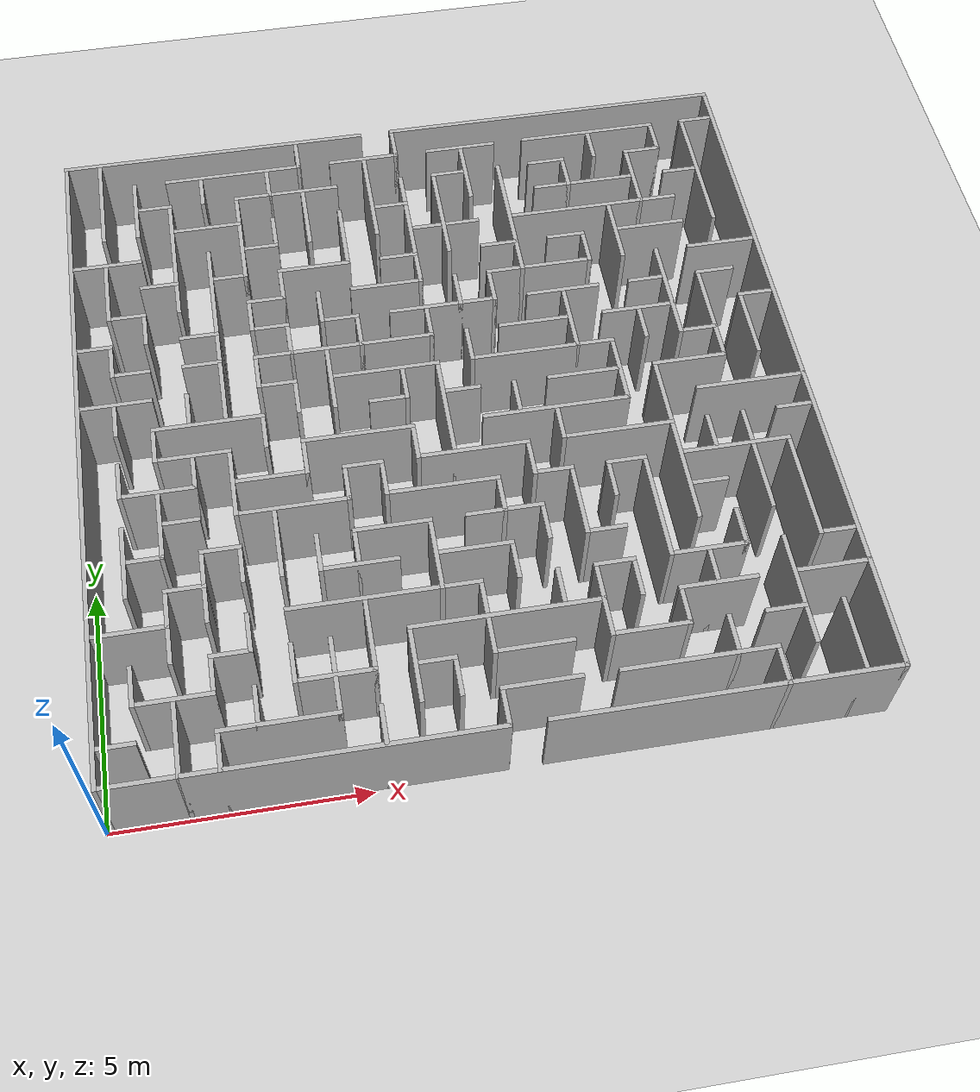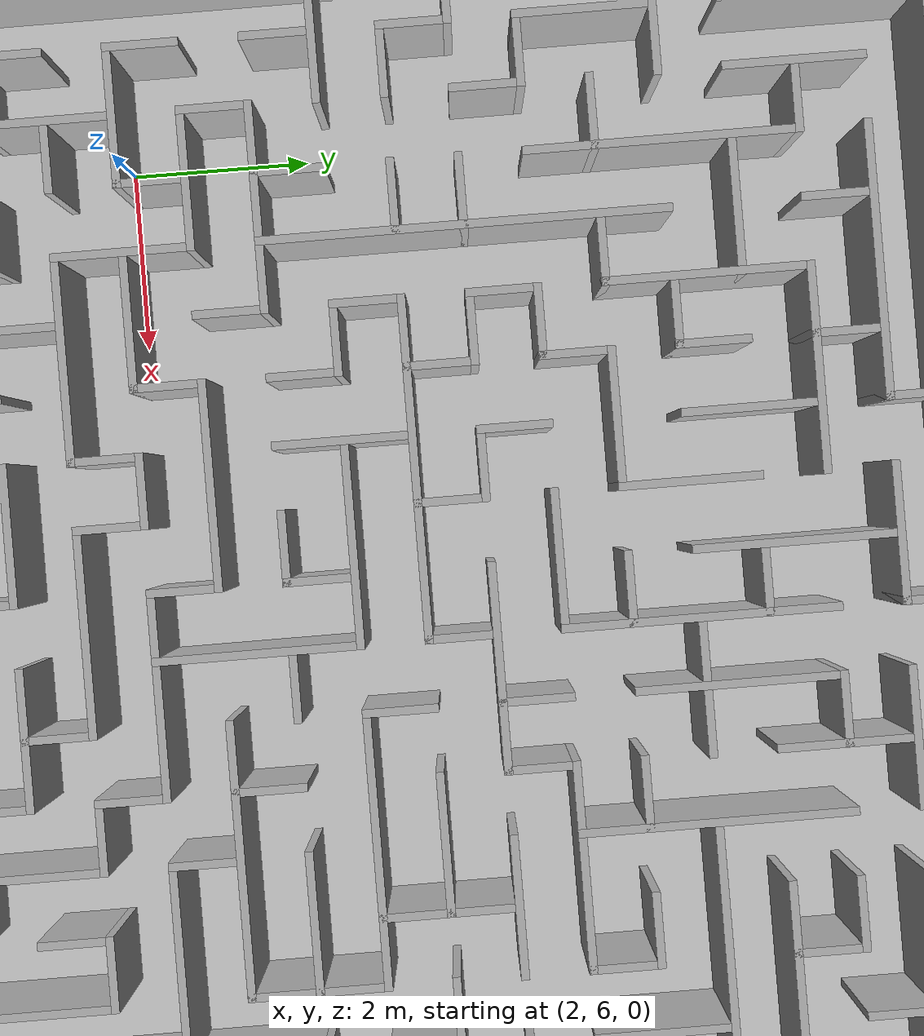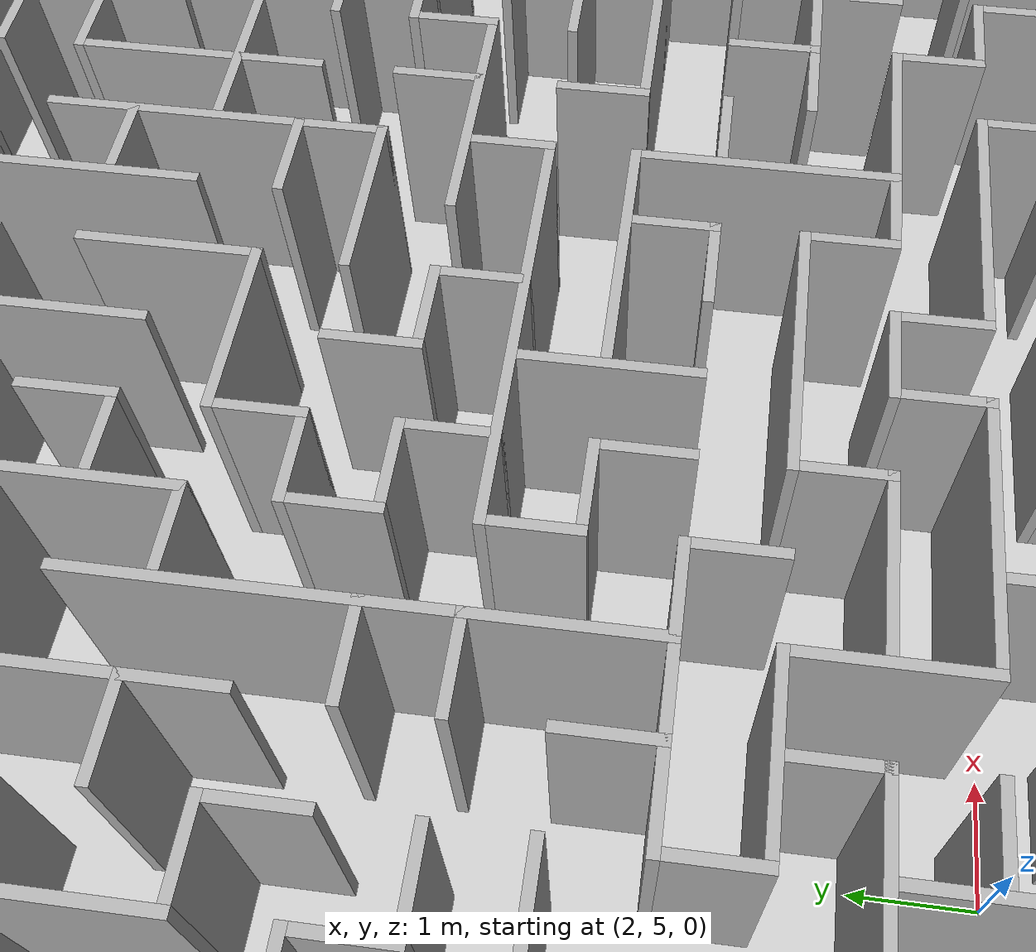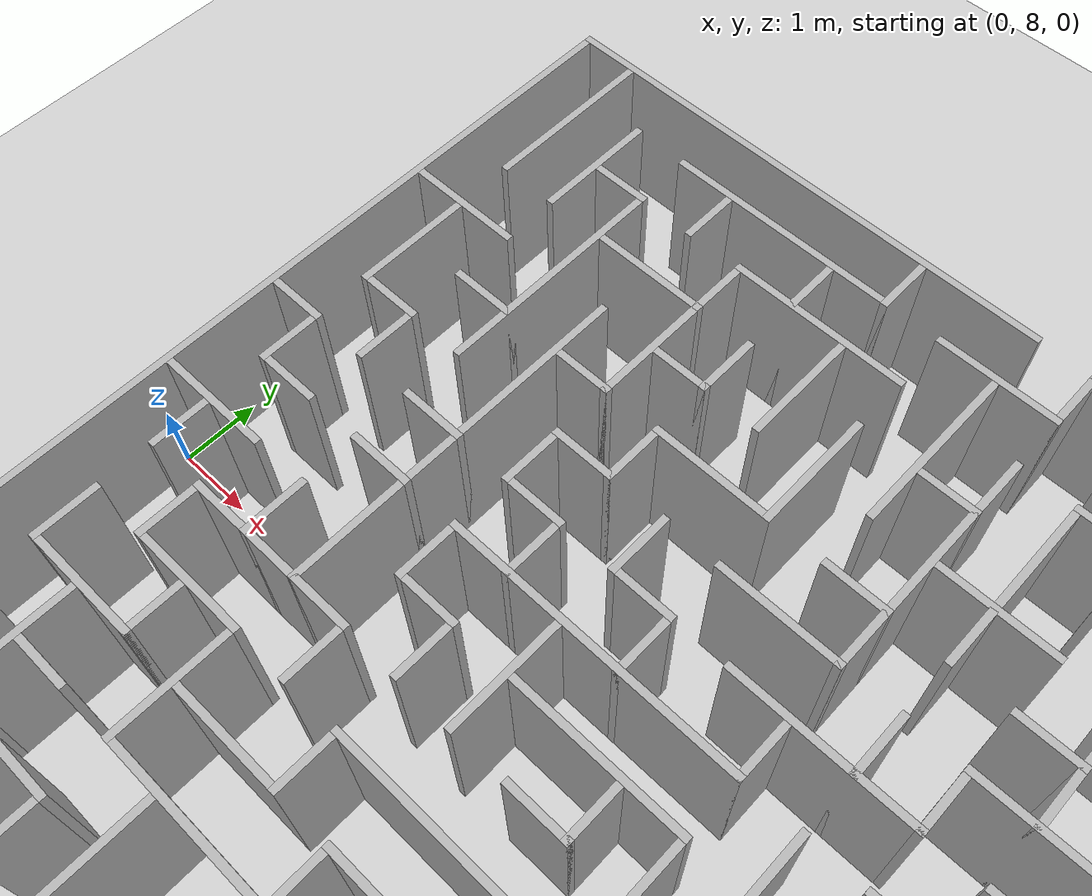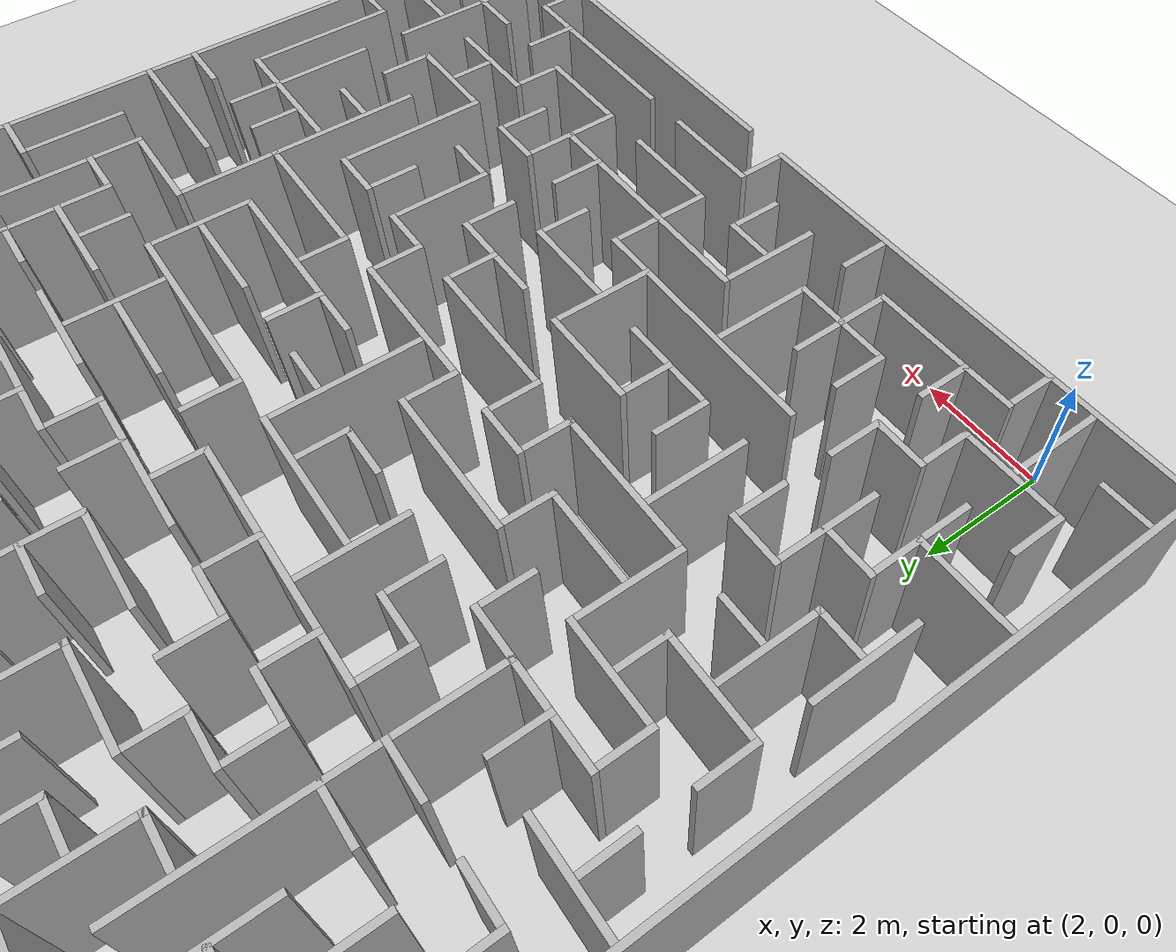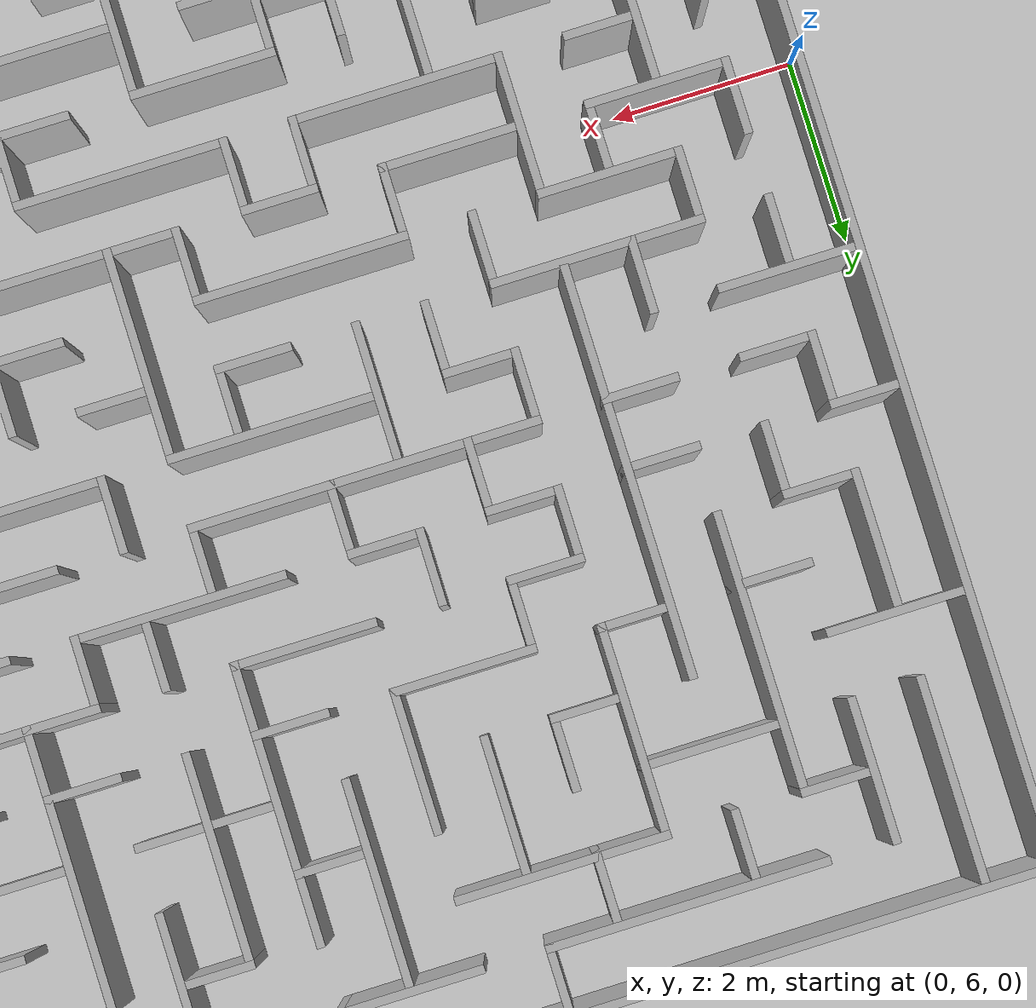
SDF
<?xml version="1.0" ?>
<sdf version="1.6">
  <world name="slam_world">
    <light name="sun" type="directional">
      <pose>0 0 10 0 0 0</pose>
      <diffuse>0.8 0.8 0.8 1</diffuse>
      <direction>-0.5 0.1 -0.9</direction>
    </light>
    <model name="ground_plane">
      <static>true</static>
      <link name="link">
        <collision name="collision">
          <geometry>
            <plane>
              <normal>0 0 1</normal>
              <size>100 100</size>
            </plane>
          </geometry>
        </collision>
        <visual name="visual">
          <geometry>
            <plane>
              <normal>0 0 1</normal>
              <size>100 100</size>
            </plane>
          </geometry>
          <material>
            <ambient>0.8 0.8 0.8 1</ambient>
            <diffuse>0.8 0.8 0.8 1</diffuse>
            <specular>0.8 0.8 0.8 1</specular>
          </material>
        </visual>
      </link>
    </model>
    <model name="wall_0">
      <static>true</static>
      <pose>3.425925925925926 14.907407407407408 1.0 0 0 0</pose>
      <link name="link">
        <collision name="collision">
          <geometry>
            <box>
              <size>6.7592592592592595 0.0925925925925926 2.0</size>
            </box>
          </geometry>
        </collision>
        <visual name="visual">
          <geometry>
            <box>
              <size>6.7592592592592595 0.0925925925925926 2.0</size>
            </box>
          </geometry>
          <material>
            <ambient>0.5 0.5 0.5 1</ambient>
            <diffuse>0.7 0.7 0.7 1</diffuse>
          </material>
        </visual>
      </link>
    </model>
    <model name="wall_1">
      <static>true</static>
      <pose>11.203703703703704 14.907407407407408 1.0 0 0 0</pose>
      <link name="link">
        <collision name="collision">
          <geometry>
            <box>
              <size>7.500000000000001 0.0925925925925926 2.0</size>
            </box>
          </geometry>
        </collision>
        <visual name="visual">
          <geometry>
            <box>
              <size>7.500000000000001 0.0925925925925926 2.0</size>
            </box>
          </geometry>
          <material>
            <ambient>0.5 0.5 0.5 1</ambient>
            <diffuse>0.7 0.7 0.7 1</diffuse>
          </material>
        </visual>
      </link>
    </model>
    <model name="wall_2">
      <static>true</static>
      <pose>0.0925925925925926 7.453703703703704 1.0 0 0 0</pose>
      <link name="link">
        <collision name="collision">
          <geometry>
            <box>
              <size>0.0925925925925926 14.814814814814817 2.0</size>
            </box>
          </geometry>
        </collision>
        <visual name="visual">
          <geometry>
            <box>
              <size>0.0925925925925926 14.814814814814817 2.0</size>
            </box>
          </geometry>
          <material>
            <ambient>0.5 0.5 0.5 1</ambient>
            <diffuse>0.7 0.7 0.7 1</diffuse>
          </material>
        </visual>
      </link>
    </model>
    <model name="wall_3">
      <static>true</static>
      <pose>0.8333333333333334 13.750000000000002 1.0 0 0 0</pose>
      <link name="link">
        <collision name="collision">
          <geometry>
            <box>
              <size>0.0925925925925926 2.2222222222222223 2.0</size>
            </box>
          </geometry>
        </collision>
        <visual name="visual">
          <geometry>
            <box>
              <size>0.0925925925925926 2.2222222222222223 2.0</size>
            </box>
          </geometry>
          <material>
            <ambient>0.5 0.5 0.5 1</ambient>
            <diffuse>0.7 0.7 0.7 1</diffuse>
          </material>
        </visual>
      </link>
    </model>
    <model name="wall_4">
      <static>true</static>
      <pose>5.277777777777779 14.490740740740742 1.0 0 0 0</pose>
      <link name="link">
        <collision name="collision">
          <geometry>
            <box>
              <size>0.0925925925925926 0.7407407407407408 2.0</size>
            </box>
          </geometry>
        </collision>
        <visual name="visual">
          <geometry>
            <box>
              <size>0.0925925925925926 0.7407407407407408 2.0</size>
            </box>
          </geometry>
          <material>
            <ambient>0.5 0.5 0.5 1</ambient>
            <diffuse>0.7 0.7 0.7 1</diffuse>
          </material>
        </visual>
      </link>
    </model>
    <model name="wall_5">
      <static>true</static>
      <pose>7.500000000000001 14.490740740740742 1.0 0 0 0</pose>
      <link name="link">
        <collision name="collision">
          <geometry>
            <box>
              <size>0.0925925925925926 0.7407407407407408 2.0</size>
            </box>
          </geometry>
        </collision>
        <visual name="visual">
          <geometry>
            <box>
              <size>0.0925925925925926 0.7407407407407408 2.0</size>
            </box>
          </geometry>
          <material>
            <ambient>0.5 0.5 0.5 1</ambient>
            <diffuse>0.7 0.7 0.7 1</diffuse>
          </material>
        </visual>
      </link>
    </model>
    <model name="wall_6">
      <static>true</static>
      <pose>14.907407407407408 7.453703703703704 1.0 0 0 0</pose>
      <link name="link">
        <collision name="collision">
          <geometry>
            <box>
              <size>0.0925925925925926 14.814814814814817 2.0</size>
            </box>
          </geometry>
        </collision>
        <visual name="visual">
          <geometry>
            <box>
              <size>0.0925925925925926 14.814814814814817 2.0</size>
            </box>
          </geometry>
          <material>
            <ambient>0.5 0.5 0.5 1</ambient>
            <diffuse>0.7 0.7 0.7 1</diffuse>
          </material>
        </visual>
      </link>
    </model>
    <model name="wall_7">
      <static>true</static>
      <pose>1.5740740740740742 13.425925925925927 1.0 0 0 0</pose>
      <link name="link">
        <collision name="collision">
          <geometry>
            <box>
              <size>0.0925925925925926 1.5740740740740742 2.0</size>
            </box>
          </geometry>
        </collision>
        <visual name="visual">
          <geometry>
            <box>
              <size>0.0925925925925926 1.5740740740740742 2.0</size>
            </box>
          </geometry>
          <material>
            <ambient>0.5 0.5 0.5 1</ambient>
            <diffuse>0.7 0.7 0.7 1</diffuse>
          </material>
        </visual>
      </link>
    </model>
    <model name="wall_8">
      <static>true</static>
      <pose>3.7962962962962967 14.166666666666668 1.0 0 0 0</pose>
      <link name="link">
        <collision name="collision">
          <geometry>
            <box>
              <size>3.055555555555556 0.0925925925925926 2.0</size>
            </box>
          </geometry>
        </collision>
        <visual name="visual">
          <geometry>
            <box>
              <size>3.055555555555556 0.0925925925925926 2.0</size>
            </box>
          </geometry>
          <material>
            <ambient>0.5 0.5 0.5 1</ambient>
            <diffuse>0.7 0.7 0.7 1</diffuse>
          </material>
        </visual>
      </link>
    </model>
    <model name="wall_9">
      <static>true</static>
      <pose>6.7592592592592595 14.166666666666668 1.0 0 0 0</pose>
      <link name="link">
        <collision name="collision">
          <geometry>
            <box>
              <size>1.5740740740740742 0.0925925925925926 2.0</size>
            </box>
          </geometry>
        </collision>
        <visual name="visual">
          <geometry>
            <box>
              <size>1.5740740740740742 0.0925925925925926 2.0</size>
            </box>
          </geometry>
          <material>
            <ambient>0.5 0.5 0.5 1</ambient>
            <diffuse>0.7 0.7 0.7 1</diffuse>
          </material>
        </visual>
      </link>
    </model>
    <model name="wall_10">
      <static>true</static>
      <pose>8.981481481481483 14.166666666666668 1.0 0 0 0</pose>
      <link name="link">
        <collision name="collision">
          <geometry>
            <box>
              <size>1.5740740740740742 0.0925925925925926 2.0</size>
            </box>
          </geometry>
        </collision>
        <visual name="visual">
          <geometry>
            <box>
              <size>1.5740740740740742 0.0925925925925926 2.0</size>
            </box>
          </geometry>
          <material>
            <ambient>0.5 0.5 0.5 1</ambient>
            <diffuse>0.7 0.7 0.7 1</diffuse>
          </material>
        </visual>
      </link>
    </model>
    <model name="wall_11">
      <static>true</static>
      <pose>11.944444444444446 14.166666666666668 1.0 0 0 0</pose>
      <link name="link">
        <collision name="collision">
          <geometry>
            <box>
              <size>3.055555555555556 0.0925925925925926 2.0</size>
            </box>
          </geometry>
        </collision>
        <visual name="visual">
          <geometry>
            <box>
              <size>3.055555555555556 0.0925925925925926 2.0</size>
            </box>
          </geometry>
          <material>
            <ambient>0.5 0.5 0.5 1</ambient>
            <diffuse>0.7 0.7 0.7 1</diffuse>
          </material>
        </visual>
      </link>
    </model>
    <model name="wall_12">
      <static>true</static>
      <pose>14.537037037037038 14.166666666666668 1.0 0 0 0</pose>
      <link name="link">
        <collision name="collision">
          <geometry>
            <box>
              <size>0.8333333333333334 0.0925925925925926 2.0</size>
            </box>
          </geometry>
        </collision>
        <visual name="visual">
          <geometry>
            <box>
              <size>0.8333333333333334 0.0925925925925926 2.0</size>
            </box>
          </geometry>
          <material>
            <ambient>0.5 0.5 0.5 1</ambient>
            <diffuse>0.7 0.7 0.7 1</diffuse>
          </material>
        </visual>
      </link>
    </model>
    <model name="wall_13">
      <static>true</static>
      <pose>3.055555555555556 13.750000000000002 1.0 0 0 0</pose>
      <link name="link">
        <collision name="collision">
          <geometry>
            <box>
              <size>0.0925925925925926 0.7407407407407408 2.0</size>
            </box>
          </geometry>
        </collision>
        <visual name="visual">
          <geometry>
            <box>
              <size>0.0925925925925926 0.7407407407407408 2.0</size>
            </box>
          </geometry>
          <material>
            <ambient>0.5 0.5 0.5 1</ambient>
            <diffuse>0.7 0.7 0.7 1</diffuse>
          </material>
        </visual>
      </link>
    </model>
    <model name="wall_14">
      <static>true</static>
      <pose>4.537037037037037 13.750000000000002 1.0 0 0 0</pose>
      <link name="link">
        <collision name="collision">
          <geometry>
            <box>
              <size>0.0925925925925926 0.7407407407407408 2.0</size>
            </box>
          </geometry>
        </collision>
        <visual name="visual">
          <geometry>
            <box>
              <size>0.0925925925925926 0.7407407407407408 2.0</size>
            </box>
          </geometry>
          <material>
            <ambient>0.5 0.5 0.5 1</ambient>
            <diffuse>0.7 0.7 0.7 1</diffuse>
          </material>
        </visual>
      </link>
    </model>
    <model name="wall_15">
      <static>true</static>
      <pose>6.7592592592592595 13.009259259259261 1.0 0 0 0</pose>
      <link name="link">
        <collision name="collision">
          <geometry>
            <box>
              <size>0.0925925925925926 2.2222222222222223 2.0</size>
            </box>
          </geometry>
        </collision>
        <visual name="visual">
          <geometry>
            <box>
              <size>0.0925925925925926 2.2222222222222223 2.0</size>
            </box>
          </geometry>
          <material>
            <ambient>0.5 0.5 0.5 1</ambient>
            <diffuse>0.7 0.7 0.7 1</diffuse>
          </material>
        </visual>
      </link>
    </model>
    <model name="wall_16">
      <static>true</static>
      <pose>8.981481481481483 13.379629629629632 1.0 0 0 0</pose>
      <link name="link">
        <collision name="collision">
          <geometry>
            <box>
              <size>0.0925925925925926 1.4814814814814816 2.0</size>
            </box>
          </geometry>
        </collision>
        <visual name="visual">
          <geometry>
            <box>
              <size>0.0925925925925926 1.4814814814814816 2.0</size>
            </box>
          </geometry>
          <material>
            <ambient>0.5 0.5 0.5 1</ambient>
            <diffuse>0.7 0.7 0.7 1</diffuse>
          </material>
        </visual>
      </link>
    </model>
    <model name="wall_17">
      <static>true</static>
      <pose>11.944444444444446 13.750000000000002 1.0 0 0 0</pose>
      <link name="link">
        <collision name="collision">
          <geometry>
            <box>
              <size>0.0925925925925926 0.7407407407407408 2.0</size>
            </box>
          </geometry>
        </collision>
        <visual name="visual">
          <geometry>
            <box>
              <size>0.0925925925925926 0.7407407407407408 2.0</size>
            </box>
          </geometry>
          <material>
            <ambient>0.5 0.5 0.5 1</ambient>
            <diffuse>0.7 0.7 0.7 1</diffuse>
          </material>
        </visual>
      </link>
    </model>
    <model name="wall_18">
      <static>true</static>
      <pose>13.425925925925927 13.750000000000002 1.0 0 0 0</pose>
      <link name="link">
        <collision name="collision">
          <geometry>
            <box>
              <size>0.0925925925925926 0.7407407407407408 2.0</size>
            </box>
          </geometry>
        </collision>
        <visual name="visual">
          <geometry>
            <box>
              <size>0.0925925925925926 0.7407407407407408 2.0</size>
            </box>
          </geometry>
          <material>
            <ambient>0.5 0.5 0.5 1</ambient>
            <diffuse>0.7 0.7 0.7 1</diffuse>
          </material>
        </visual>
      </link>
    </model>
    <model name="wall_19">
      <static>true</static>
      <pose>14.166666666666668 12.63888888888889 1.0 0 0 0</pose>
      <link name="link">
        <collision name="collision">
          <geometry>
            <box>
              <size>0.0925925925925926 2.9629629629629632 2.0</size>
            </box>
          </geometry>
        </collision>
        <visual name="visual">
          <geometry>
            <box>
              <size>0.0925925925925926 2.9629629629629632 2.0</size>
            </box>
          </geometry>
          <material>
            <ambient>0.5 0.5 0.5 1</ambient>
            <diffuse>0.7 0.7 0.7 1</diffuse>
          </material>
        </visual>
      </link>
    </model>
    <model name="wall_20">
      <static>true</static>
      <pose>1.990740740740741 13.425925925925927 1.0 0 0 0</pose>
      <link name="link">
        <collision name="collision">
          <geometry>
            <box>
              <size>0.7407407407407408 0.0925925925925926 2.0</size>
            </box>
          </geometry>
        </collision>
        <visual name="visual">
          <geometry>
            <box>
              <size>0.7407407407407408 0.0925925925925926 2.0</size>
            </box>
          </geometry>
          <material>
            <ambient>0.5 0.5 0.5 1</ambient>
            <diffuse>0.7 0.7 0.7 1</diffuse>
          </material>
        </visual>
      </link>
    </model>
    <model name="wall_21">
      <static>true</static>
      <pose>4.907407407407407 13.425925925925927 1.0 0 0 0</pose>
      <link name="link">
        <collision name="collision">
          <geometry>
            <box>
              <size>2.314814814814815 0.0925925925925926 2.0</size>
            </box>
          </geometry>
        </collision>
        <visual name="visual">
          <geometry>
            <box>
              <size>2.314814814814815 0.0925925925925926 2.0</size>
            </box>
          </geometry>
          <material>
            <ambient>0.5 0.5 0.5 1</ambient>
            <diffuse>0.7 0.7 0.7 1</diffuse>
          </material>
        </visual>
      </link>
    </model>
    <model name="wall_22">
      <static>true</static>
      <pose>7.500000000000001 11.944444444444446 1.0 0 0 0</pose>
      <link name="link">
        <collision name="collision">
          <geometry>
            <box>
              <size>0.0925925925925926 3.055555555555556 2.0</size>
            </box>
          </geometry>
        </collision>
        <visual name="visual">
          <geometry>
            <box>
              <size>0.0925925925925926 3.055555555555556 2.0</size>
            </box>
          </geometry>
          <material>
            <ambient>0.5 0.5 0.5 1</ambient>
            <diffuse>0.7 0.7 0.7 1</diffuse>
          </material>
        </visual>
      </link>
    </model>
    <model name="wall_23">
      <static>true</static>
      <pose>8.611111111111112 13.425925925925927 1.0 0 0 0</pose>
      <link name="link">
        <collision name="collision">
          <geometry>
            <box>
              <size>0.8333333333333334 0.0925925925925926 2.0</size>
            </box>
          </geometry>
        </collision>
        <visual name="visual">
          <geometry>
            <box>
              <size>0.8333333333333334 0.0925925925925926 2.0</size>
            </box>
          </geometry>
          <material>
            <ambient>0.5 0.5 0.5 1</ambient>
            <diffuse>0.7 0.7 0.7 1</diffuse>
          </material>
        </visual>
      </link>
    </model>
    <model name="wall_24">
      <static>true</static>
      <pose>9.722222222222223 11.944444444444446 1.0 0 0 0</pose>
      <link name="link">
        <collision name="collision">
          <geometry>
            <box>
              <size>0.0925925925925926 3.055555555555556 2.0</size>
            </box>
          </geometry>
        </collision>
        <visual name="visual">
          <geometry>
            <box>
              <size>0.0925925925925926 3.055555555555556 2.0</size>
            </box>
          </geometry>
          <material>
            <ambient>0.5 0.5 0.5 1</ambient>
            <diffuse>0.7 0.7 0.7 1</diffuse>
          </material>
        </visual>
      </link>
    </model>
    <model name="wall_25">
      <static>true</static>
      <pose>10.833333333333334 13.425925925925927 1.0 0 0 0</pose>
      <link name="link">
        <collision name="collision">
          <geometry>
            <box>
              <size>0.8333333333333334 0.0925925925925926 2.0</size>
            </box>
          </geometry>
        </collision>
        <visual name="visual">
          <geometry>
            <box>
              <size>0.8333333333333334 0.0925925925925926 2.0</size>
            </box>
          </geometry>
          <material>
            <ambient>0.5 0.5 0.5 1</ambient>
            <diffuse>0.7 0.7 0.7 1</diffuse>
          </material>
        </visual>
      </link>
    </model>
    <model name="wall_26">
      <static>true</static>
      <pose>13.055555555555557 13.425925925925927 1.0 0 0 0</pose>
      <link name="link">
        <collision name="collision">
          <geometry>
            <box>
              <size>0.8333333333333334 0.0925925925925926 2.0</size>
            </box>
          </geometry>
        </collision>
        <visual name="visual">
          <geometry>
            <box>
              <size>0.8333333333333334 0.0925925925925926 2.0</size>
            </box>
          </geometry>
          <material>
            <ambient>0.5 0.5 0.5 1</ambient>
            <diffuse>0.7 0.7 0.7 1</diffuse>
          </material>
        </visual>
      </link>
    </model>
    <model name="wall_27">
      <static>true</static>
      <pose>2.314814814814815 11.898148148148149 1.0 0 0 0</pose>
      <link name="link">
        <collision name="collision">
          <geometry>
            <box>
              <size>0.0925925925925926 2.9629629629629632 2.0</size>
            </box>
          </geometry>
        </collision>
        <visual name="visual">
          <geometry>
            <box>
              <size>0.0925925925925926 2.9629629629629632 2.0</size>
            </box>
          </geometry>
          <material>
            <ambient>0.5 0.5 0.5 1</ambient>
            <diffuse>0.7 0.7 0.7 1</diffuse>
          </material>
        </visual>
      </link>
    </model>
    <model name="wall_28">
      <static>true</static>
      <pose>3.7962962962962967 12.268518518518519 1.0 0 0 0</pose>
      <link name="link">
        <collision name="collision">
          <geometry>
            <box>
              <size>0.0925925925925926 2.2222222222222223 2.0</size>
            </box>
          </geometry>
        </collision>
        <visual name="visual">
          <geometry>
            <box>
              <size>0.0925925925925926 2.2222222222222223 2.0</size>
            </box>
          </geometry>
          <material>
            <ambient>0.5 0.5 0.5 1</ambient>
            <diffuse>0.7 0.7 0.7 1</diffuse>
          </material>
        </visual>
      </link>
    </model>
    <model name="wall_29">
      <static>true</static>
      <pose>5.277777777777779 12.63888888888889 1.0 0 0 0</pose>
      <link name="link">
        <collision name="collision">
          <geometry>
            <box>
              <size>0.0925925925925926 1.4814814814814816 2.0</size>
            </box>
          </geometry>
        </collision>
        <visual name="visual">
          <geometry>
            <box>
              <size>0.0925925925925926 1.4814814814814816 2.0</size>
            </box>
          </geometry>
          <material>
            <ambient>0.5 0.5 0.5 1</ambient>
            <diffuse>0.7 0.7 0.7 1</diffuse>
          </material>
        </visual>
      </link>
    </model>
    <model name="wall_30">
      <static>true</static>
      <pose>8.240740740740742 12.268518518518519 1.0 0 0 0</pose>
      <link name="link">
        <collision name="collision">
          <geometry>
            <box>
              <size>0.0925925925925926 2.2222222222222223 2.0</size>
            </box>
          </geometry>
        </collision>
        <visual name="visual">
          <geometry>
            <box>
              <size>0.0925925925925926 2.2222222222222223 2.0</size>
            </box>
          </geometry>
          <material>
            <ambient>0.5 0.5 0.5 1</ambient>
            <diffuse>0.7 0.7 0.7 1</diffuse>
          </material>
        </visual>
      </link>
    </model>
    <model name="wall_31">
      <static>true</static>
      <pose>11.203703703703704 13.009259259259261 1.0 0 0 0</pose>
      <link name="link">
        <collision name="collision">
          <geometry>
            <box>
              <size>0.0925925925925926 0.7407407407407408 2.0</size>
            </box>
          </geometry>
        </collision>
        <visual name="visual">
          <geometry>
            <box>
              <size>0.0925925925925926 0.7407407407407408 2.0</size>
            </box>
          </geometry>
          <material>
            <ambient>0.5 0.5 0.5 1</ambient>
            <diffuse>0.7 0.7 0.7 1</diffuse>
          </material>
        </visual>
      </link>
    </model>
    <model name="wall_32">
      <static>true</static>
      <pose>12.685185185185187 12.63888888888889 1.0 0 0 0</pose>
      <link name="link">
        <collision name="collision">
          <geometry>
            <box>
              <size>0.0925925925925926 1.4814814814814816 2.0</size>
            </box>
          </geometry>
        </collision>
        <visual name="visual">
          <geometry>
            <box>
              <size>0.0925925925925926 1.4814814814814816 2.0</size>
            </box>
          </geometry>
          <material>
            <ambient>0.5 0.5 0.5 1</ambient>
            <diffuse>0.7 0.7 0.7 1</diffuse>
          </material>
        </visual>
      </link>
    </model>
    <model name="wall_33">
      <static>true</static>
      <pose>3.101851851851852 12.685185185185187 1.0 0 0 0</pose>
      <link name="link">
        <collision name="collision">
          <geometry>
            <box>
              <size>1.4814814814814816 0.0925925925925926 2.0</size>
            </box>
          </geometry>
        </collision>
        <visual name="visual">
          <geometry>
            <box>
              <size>1.4814814814814816 0.0925925925925926 2.0</size>
            </box>
          </geometry>
          <material>
            <ambient>0.5 0.5 0.5 1</ambient>
            <diffuse>0.7 0.7 0.7 1</diffuse>
          </material>
        </visual>
      </link>
    </model>
    <model name="wall_34">
      <static>true</static>
      <pose>4.537037037037037 12.314814814814817 1.0 0 0 0</pose>
      <link name="link">
        <collision name="collision">
          <geometry>
            <box>
              <size>0.0925925925925926 0.8333333333333334 2.0</size>
            </box>
          </geometry>
        </collision>
        <visual name="visual">
          <geometry>
            <box>
              <size>0.0925925925925926 0.8333333333333334 2.0</size>
            </box>
          </geometry>
          <material>
            <ambient>0.5 0.5 0.5 1</ambient>
            <diffuse>0.7 0.7 0.7 1</diffuse>
          </material>
        </visual>
      </link>
    </model>
    <model name="wall_35">
      <static>true</static>
      <pose>6.018518518518519 11.944444444444446 1.0 0 0 0</pose>
      <link name="link">
        <collision name="collision">
          <geometry>
            <box>
              <size>0.0925925925925926 1.5740740740740742 2.0</size>
            </box>
          </geometry>
        </collision>
        <visual name="visual">
          <geometry>
            <box>
              <size>0.0925925925925926 1.5740740740740742 2.0</size>
            </box>
          </geometry>
          <material>
            <ambient>0.5 0.5 0.5 1</ambient>
            <diffuse>0.7 0.7 0.7 1</diffuse>
          </material>
        </visual>
      </link>
    </model>
    <model name="wall_36">
      <static>true</static>
      <pose>7.1759259259259265 12.685185185185187 1.0 0 0 0</pose>
      <link name="link">
        <collision name="collision">
          <geometry>
            <box>
              <size>0.7407407407407408 0.0925925925925926 2.0</size>
            </box>
          </geometry>
        </collision>
        <visual name="visual">
          <geometry>
            <box>
              <size>0.7407407407407408 0.0925925925925926 2.0</size>
            </box>
          </geometry>
          <material>
            <ambient>0.5 0.5 0.5 1</ambient>
            <diffuse>0.7 0.7 0.7 1</diffuse>
          </material>
        </visual>
      </link>
    </model>
    <model name="wall_37">
      <static>true</static>
      <pose>11.574074074074074 12.685185185185187 1.0 0 0 0</pose>
      <link name="link">
        <collision name="collision">
          <geometry>
            <box>
              <size>2.314814814814815 0.0925925925925926 2.0</size>
            </box>
          </geometry>
        </collision>
        <visual name="visual">
          <geometry>
            <box>
              <size>2.314814814814815 0.0925925925925926 2.0</size>
            </box>
          </geometry>
          <material>
            <ambient>0.5 0.5 0.5 1</ambient>
            <diffuse>0.7 0.7 0.7 1</diffuse>
          </material>
        </visual>
      </link>
    </model>
    <model name="wall_38">
      <static>true</static>
      <pose>13.796296296296298 12.685185185185187 1.0 0 0 0</pose>
      <link name="link">
        <collision name="collision">
          <geometry>
            <box>
              <size>0.8333333333333334 0.0925925925925926 2.0</size>
            </box>
          </geometry>
        </collision>
        <visual name="visual">
          <geometry>
            <box>
              <size>0.8333333333333334 0.0925925925925926 2.0</size>
            </box>
          </geometry>
          <material>
            <ambient>0.5 0.5 0.5 1</ambient>
            <diffuse>0.7 0.7 0.7 1</diffuse>
          </material>
        </visual>
      </link>
    </model>
    <model name="wall_39">
      <static>true</static>
      <pose>0.8796296296296298 11.944444444444446 1.0 0 0 0</pose>
      <link name="link">
        <collision name="collision">
          <geometry>
            <box>
              <size>1.4814814814814816 0.0925925925925926 2.0</size>
            </box>
          </geometry>
        </collision>
        <visual name="visual">
          <geometry>
            <box>
              <size>1.4814814814814816 0.0925925925925926 2.0</size>
            </box>
          </geometry>
          <material>
            <ambient>0.5 0.5 0.5 1</ambient>
            <diffuse>0.7 0.7 0.7 1</diffuse>
          </material>
        </visual>
      </link>
    </model>
    <model name="wall_40">
      <static>true</static>
      <pose>3.055555555555556 9.722222222222223 1.0 0 0 0</pose>
      <link name="link">
        <collision name="collision">
          <geometry>
            <box>
              <size>0.0925925925925926 4.537037037037037 2.0</size>
            </box>
          </geometry>
        </collision>
        <visual name="visual">
          <geometry>
            <box>
              <size>0.0925925925925926 4.537037037037037 2.0</size>
            </box>
          </geometry>
          <material>
            <ambient>0.5 0.5 0.5 1</ambient>
            <diffuse>0.7 0.7 0.7 1</diffuse>
          </material>
        </visual>
      </link>
    </model>
    <model name="wall_41">
      <static>true</static>
      <pose>4.212962962962964 11.944444444444446 1.0 0 0 0</pose>
      <link name="link">
        <collision name="collision">
          <geometry>
            <box>
              <size>0.7407407407407408 0.0925925925925926 2.0</size>
            </box>
          </geometry>
        </collision>
        <visual name="visual">
          <geometry>
            <box>
              <size>0.7407407407407408 0.0925925925925926 2.0</size>
            </box>
          </geometry>
          <material>
            <ambient>0.5 0.5 0.5 1</ambient>
            <diffuse>0.7 0.7 0.7 1</diffuse>
          </material>
        </visual>
      </link>
    </model>
    <model name="wall_42">
      <static>true</static>
      <pose>8.287037037037038 11.944444444444446 1.0 0 0 0</pose>
      <link name="link">
        <collision name="collision">
          <geometry>
            <box>
              <size>1.4814814814814816 0.0925925925925926 2.0</size>
            </box>
          </geometry>
        </collision>
        <visual name="visual">
          <geometry>
            <box>
              <size>1.4814814814814816 0.0925925925925926 2.0</size>
            </box>
          </geometry>
          <material>
            <ambient>0.5 0.5 0.5 1</ambient>
            <diffuse>0.7 0.7 0.7 1</diffuse>
          </material>
        </visual>
      </link>
    </model>
    <model name="wall_43">
      <static>true</static>
      <pose>11.620370370370372 11.944444444444446 1.0 0 0 0</pose>
      <link name="link">
        <collision name="collision">
          <geometry>
            <box>
              <size>3.703703703703704 0.0925925925925926 2.0</size>
            </box>
          </geometry>
        </collision>
        <visual name="visual">
          <geometry>
            <box>
              <size>3.703703703703704 0.0925925925925926 2.0</size>
            </box>
          </geometry>
          <material>
            <ambient>0.5 0.5 0.5 1</ambient>
            <diffuse>0.7 0.7 0.7 1</diffuse>
          </material>
        </visual>
      </link>
    </model>
    <model name="wall_44">
      <static>true</static>
      <pose>0.8333333333333334 11.157407407407408 1.0 0 0 0</pose>
      <link name="link">
        <collision name="collision">
          <geometry>
            <box>
              <size>0.0925925925925926 1.4814814814814816 2.0</size>
            </box>
          </geometry>
        </collision>
        <visual name="visual">
          <geometry>
            <box>
              <size>0.0925925925925926 1.4814814814814816 2.0</size>
            </box>
          </geometry>
          <material>
            <ambient>0.5 0.5 0.5 1</ambient>
            <diffuse>0.7 0.7 0.7 1</diffuse>
          </material>
        </visual>
      </link>
    </model>
    <model name="wall_45">
      <static>true</static>
      <pose>11.944444444444446 11.157407407407408 1.0 0 0 0</pose>
      <link name="link">
        <collision name="collision">
          <geometry>
            <box>
              <size>0.0925925925925926 1.4814814814814816 2.0</size>
            </box>
          </geometry>
        </collision>
        <visual name="visual">
          <geometry>
            <box>
              <size>0.0925925925925926 1.4814814814814816 2.0</size>
            </box>
          </geometry>
          <material>
            <ambient>0.5 0.5 0.5 1</ambient>
            <diffuse>0.7 0.7 0.7 1</diffuse>
          </material>
        </visual>
      </link>
    </model>
    <model name="wall_46">
      <static>true</static>
      <pose>1.9444444444444446 11.203703703703704 1.0 0 0 0</pose>
      <link name="link">
        <collision name="collision">
          <geometry>
            <box>
              <size>0.8333333333333334 0.0925925925925926 2.0</size>
            </box>
          </geometry>
        </collision>
        <visual name="visual">
          <geometry>
            <box>
              <size>0.8333333333333334 0.0925925925925926 2.0</size>
            </box>
          </geometry>
          <material>
            <ambient>0.5 0.5 0.5 1</ambient>
            <diffuse>0.7 0.7 0.7 1</diffuse>
          </material>
        </visual>
      </link>
    </model>
    <model name="wall_47">
      <static>true</static>
      <pose>3.4722222222222228 11.203703703703704 1.0 0 0 0</pose>
      <link name="link">
        <collision name="collision">
          <geometry>
            <box>
              <size>0.7407407407407408 0.0925925925925926 2.0</size>
            </box>
          </geometry>
        </collision>
        <visual name="visual">
          <geometry>
            <box>
              <size>0.7407407407407408 0.0925925925925926 2.0</size>
            </box>
          </geometry>
          <material>
            <ambient>0.5 0.5 0.5 1</ambient>
            <diffuse>0.7 0.7 0.7 1</diffuse>
          </material>
        </visual>
      </link>
    </model>
    <model name="wall_48">
      <static>true</static>
      <pose>5.277777777777779 11.203703703703704 1.0 0 0 0</pose>
      <link name="link">
        <collision name="collision">
          <geometry>
            <box>
              <size>1.5740740740740742 0.0925925925925926 2.0</size>
            </box>
          </geometry>
        </collision>
        <visual name="visual">
          <geometry>
            <box>
              <size>1.5740740740740742 0.0925925925925926 2.0</size>
            </box>
          </geometry>
          <material>
            <ambient>0.5 0.5 0.5 1</ambient>
            <diffuse>0.7 0.7 0.7 1</diffuse>
          </material>
        </visual>
      </link>
    </model>
    <model name="wall_49">
      <static>true</static>
      <pose>7.129629629629631 11.203703703703704 1.0 0 0 0</pose>
      <link name="link">
        <collision name="collision">
          <geometry>
            <box>
              <size>0.8333333333333334 0.0925925925925926 2.0</size>
            </box>
          </geometry>
        </collision>
        <visual name="visual">
          <geometry>
            <box>
              <size>0.8333333333333334 0.0925925925925926 2.0</size>
            </box>
          </geometry>
          <material>
            <ambient>0.5 0.5 0.5 1</ambient>
            <diffuse>0.7 0.7 0.7 1</diffuse>
          </material>
        </visual>
      </link>
    </model>
    <model name="wall_50">
      <static>true</static>
      <pose>9.351851851851853 11.203703703703704 1.0 0 0 0</pose>
      <link name="link">
        <collision name="collision">
          <geometry>
            <box>
              <size>0.8333333333333334 0.0925925925925926 2.0</size>
            </box>
          </geometry>
        </collision>
        <visual name="visual">
          <geometry>
            <box>
              <size>0.8333333333333334 0.0925925925925926 2.0</size>
            </box>
          </geometry>
          <material>
            <ambient>0.5 0.5 0.5 1</ambient>
            <diffuse>0.7 0.7 0.7 1</diffuse>
          </material>
        </visual>
      </link>
    </model>
    <model name="wall_51">
      <static>true</static>
      <pose>10.833333333333334 11.203703703703704 1.0 0 0 0</pose>
      <link name="link">
        <collision name="collision">
          <geometry>
            <box>
              <size>0.8333333333333334 0.0925925925925926 2.0</size>
            </box>
          </geometry>
        </collision>
        <visual name="visual">
          <geometry>
            <box>
              <size>0.8333333333333334 0.0925925925925926 2.0</size>
            </box>
          </geometry>
          <material>
            <ambient>0.5 0.5 0.5 1</ambient>
            <diffuse>0.7 0.7 0.7 1</diffuse>
          </material>
        </visual>
      </link>
    </model>
    <model name="wall_52">
      <static>true</static>
      <pose>12.731481481481483 11.203703703703704 1.0 0 0 0</pose>
      <link name="link">
        <collision name="collision">
          <geometry>
            <box>
              <size>1.4814814814814816 0.0925925925925926 2.0</size>
            </box>
          </geometry>
        </collision>
        <visual name="visual">
          <geometry>
            <box>
              <size>1.4814814814814816 0.0925925925925926 2.0</size>
            </box>
          </geometry>
          <material>
            <ambient>0.5 0.5 0.5 1</ambient>
            <diffuse>0.7 0.7 0.7 1</diffuse>
          </material>
        </visual>
      </link>
    </model>
    <model name="wall_53">
      <static>true</static>
      <pose>4.537037037037037 10.787037037037038 1.0 0 0 0</pose>
      <link name="link">
        <collision name="collision">
          <geometry>
            <box>
              <size>0.0925925925925926 0.7407407407407408 2.0</size>
            </box>
          </geometry>
        </collision>
        <visual name="visual">
          <geometry>
            <box>
              <size>0.0925925925925926 0.7407407407407408 2.0</size>
            </box>
          </geometry>
          <material>
            <ambient>0.5 0.5 0.5 1</ambient>
            <diffuse>0.7 0.7 0.7 1</diffuse>
          </material>
        </visual>
      </link>
    </model>
    <model name="wall_54">
      <static>true</static>
      <pose>11.203703703703704 10.787037037037038 1.0 0 0 0</pose>
      <link name="link">
        <collision name="collision">
          <geometry>
            <box>
              <size>0.0925925925925926 0.7407407407407408 2.0</size>
            </box>
          </geometry>
        </collision>
        <visual name="visual">
          <geometry>
            <box>
              <size>0.0925925925925926 0.7407407407407408 2.0</size>
            </box>
          </geometry>
          <material>
            <ambient>0.5 0.5 0.5 1</ambient>
            <diffuse>0.7 0.7 0.7 1</diffuse>
          </material>
        </visual>
      </link>
    </model>
    <model name="wall_55">
      <static>true</static>
      <pose>1.2500000000000002 10.462962962962964 1.0 0 0 0</pose>
      <link name="link">
        <collision name="collision">
          <geometry>
            <box>
              <size>0.7407407407407408 0.0925925925925926 2.0</size>
            </box>
          </geometry>
        </collision>
        <visual name="visual">
          <geometry>
            <box>
              <size>0.7407407407407408 0.0925925925925926 2.0</size>
            </box>
          </geometry>
          <material>
            <ambient>0.5 0.5 0.5 1</ambient>
            <diffuse>0.7 0.7 0.7 1</diffuse>
          </material>
        </visual>
      </link>
    </model>
    <model name="wall_56">
      <static>true</static>
      <pose>4.166666666666667 10.462962962962964 1.0 0 0 0</pose>
      <link name="link">
        <collision name="collision">
          <geometry>
            <box>
              <size>0.8333333333333334 0.0925925925925926 2.0</size>
            </box>
          </geometry>
        </collision>
        <visual name="visual">
          <geometry>
            <box>
              <size>0.8333333333333334 0.0925925925925926 2.0</size>
            </box>
          </geometry>
          <material>
            <ambient>0.5 0.5 0.5 1</ambient>
            <diffuse>0.7 0.7 0.7 1</diffuse>
          </material>
        </visual>
      </link>
    </model>
    <model name="wall_57">
      <static>true</static>
      <pose>5.277777777777779 10.092592592592593 1.0 0 0 0</pose>
      <link name="link">
        <collision name="collision">
          <geometry>
            <box>
              <size>0.0925925925925926 0.8333333333333334 2.0</size>
            </box>
          </geometry>
        </collision>
        <visual name="visual">
          <geometry>
            <box>
              <size>0.0925925925925926 0.8333333333333334 2.0</size>
            </box>
          </geometry>
          <material>
            <ambient>0.5 0.5 0.5 1</ambient>
            <diffuse>0.7 0.7 0.7 1</diffuse>
          </material>
        </visual>
      </link>
    </model>
    <model name="wall_58">
      <static>true</static>
      <pose>6.7592592592592595 10.462962962962964 1.0 0 0 0</pose>
      <link name="link">
        <collision name="collision">
          <geometry>
            <box>
              <size>1.5740740740740742 0.0925925925925926 2.0</size>
            </box>
          </geometry>
        </collision>
        <visual name="visual">
          <geometry>
            <box>
              <size>1.5740740740740742 0.0925925925925926 2.0</size>
            </box>
          </geometry>
          <material>
            <ambient>0.5 0.5 0.5 1</ambient>
            <diffuse>0.7 0.7 0.7 1</diffuse>
          </material>
        </visual>
      </link>
    </model>
    <model name="wall_59">
      <static>true</static>
      <pose>8.240740740740742 10.092592592592593 1.0 0 0 0</pose>
      <link name="link">
        <collision name="collision">
          <geometry>
            <box>
              <size>0.0925925925925926 0.8333333333333334 2.0</size>
            </box>
          </geometry>
        </collision>
        <visual name="visual">
          <geometry>
            <box>
              <size>0.0925925925925926 0.8333333333333334 2.0</size>
            </box>
          </geometry>
          <material>
            <ambient>0.5 0.5 0.5 1</ambient>
            <diffuse>0.7 0.7 0.7 1</diffuse>
          </material>
        </visual>
      </link>
    </model>
    <model name="wall_60">
      <static>true</static>
      <pose>10.092592592592593 10.462962962962964 1.0 0 0 0</pose>
      <link name="link">
        <collision name="collision">
          <geometry>
            <box>
              <size>2.314814814814815 0.0925925925925926 2.0</size>
            </box>
          </geometry>
        </collision>
        <visual name="visual">
          <geometry>
            <box>
              <size>2.314814814814815 0.0925925925925926 2.0</size>
            </box>
          </geometry>
          <material>
            <ambient>0.5 0.5 0.5 1</ambient>
            <diffuse>0.7 0.7 0.7 1</diffuse>
          </material>
        </visual>
      </link>
    </model>
    <model name="wall_61">
      <static>true</static>
      <pose>12.685185185185187 9.351851851851853 1.0 0 0 0</pose>
      <link name="link">
        <collision name="collision">
          <geometry>
            <box>
              <size>0.0925925925925926 2.314814814814815 2.0</size>
            </box>
          </geometry>
        </collision>
        <visual name="visual">
          <geometry>
            <box>
              <size>0.0925925925925926 2.314814814814815 2.0</size>
            </box>
          </geometry>
          <material>
            <ambient>0.5 0.5 0.5 1</ambient>
            <diffuse>0.7 0.7 0.7 1</diffuse>
          </material>
        </visual>
      </link>
    </model>
    <model name="wall_62">
      <static>true</static>
      <pose>14.166666666666668 10.462962962962964 1.0 0 0 0</pose>
      <link name="link">
        <collision name="collision">
          <geometry>
            <box>
              <size>1.5740740740740742 0.0925925925925926 2.0</size>
            </box>
          </geometry>
        </collision>
        <visual name="visual">
          <geometry>
            <box>
              <size>1.5740740740740742 0.0925925925925926 2.0</size>
            </box>
          </geometry>
          <material>
            <ambient>0.5 0.5 0.5 1</ambient>
            <diffuse>0.7 0.7 0.7 1</diffuse>
          </material>
        </visual>
      </link>
    </model>
    <model name="wall_63">
      <static>true</static>
      <pose>1.5740740740740742 10.046296296296298 1.0 0 0 0</pose>
      <link name="link">
        <collision name="collision">
          <geometry>
            <box>
              <size>0.0925925925925926 0.7407407407407408 2.0</size>
            </box>
          </geometry>
        </collision>
        <visual name="visual">
          <geometry>
            <box>
              <size>0.0925925925925926 0.7407407407407408 2.0</size>
            </box>
          </geometry>
          <material>
            <ambient>0.5 0.5 0.5 1</ambient>
            <diffuse>0.7 0.7 0.7 1</diffuse>
          </material>
        </visual>
      </link>
    </model>
    <model name="wall_64">
      <static>true</static>
      <pose>3.7962962962962967 10.046296296296298 1.0 0 0 0</pose>
      <link name="link">
        <collision name="collision">
          <geometry>
            <box>
              <size>0.0925925925925926 0.7407407407407408 2.0</size>
            </box>
          </geometry>
        </collision>
        <visual name="visual">
          <geometry>
            <box>
              <size>0.0925925925925926 0.7407407407407408 2.0</size>
            </box>
          </geometry>
          <material>
            <ambient>0.5 0.5 0.5 1</ambient>
            <diffuse>0.7 0.7 0.7 1</diffuse>
          </material>
        </visual>
      </link>
    </model>
    <model name="wall_65">
      <static>true</static>
      <pose>8.981481481481483 10.046296296296298 1.0 0 0 0</pose>
      <link name="link">
        <collision name="collision">
          <geometry>
            <box>
              <size>0.0925925925925926 0.7407407407407408 2.0</size>
            </box>
          </geometry>
        </collision>
        <visual name="visual">
          <geometry>
            <box>
              <size>0.0925925925925926 0.7407407407407408 2.0</size>
            </box>
          </geometry>
          <material>
            <ambient>0.5 0.5 0.5 1</ambient>
            <diffuse>0.7 0.7 0.7 1</diffuse>
          </material>
        </visual>
      </link>
    </model>
    <model name="wall_66">
      <static>true</static>
      <pose>0.5092592592592593 9.722222222222223 1.0 0 0 0</pose>
      <link name="link">
        <collision name="collision">
          <geometry>
            <box>
              <size>0.7407407407407408 0.0925925925925926 2.0</size>
            </box>
          </geometry>
        </collision>
        <visual name="visual">
          <geometry>
            <box>
              <size>0.7407407407407408 0.0925925925925926 2.0</size>
            </box>
          </geometry>
          <material>
            <ambient>0.5 0.5 0.5 1</ambient>
            <diffuse>0.7 0.7 0.7 1</diffuse>
          </material>
        </visual>
      </link>
    </model>
    <model name="wall_67">
      <static>true</static>
      <pose>2.6851851851851856 9.722222222222223 1.0 0 0 0</pose>
      <link name="link">
        <collision name="collision">
          <geometry>
            <box>
              <size>0.8333333333333334 0.0925925925925926 2.0</size>
            </box>
          </geometry>
        </collision>
        <visual name="visual">
          <geometry>
            <box>
              <size>0.8333333333333334 0.0925925925925926 2.0</size>
            </box>
          </geometry>
          <material>
            <ambient>0.5 0.5 0.5 1</ambient>
            <diffuse>0.7 0.7 0.7 1</diffuse>
          </material>
        </visual>
      </link>
    </model>
    <model name="wall_68">
      <static>true</static>
      <pose>4.212962962962964 9.722222222222223 1.0 0 0 0</pose>
      <link name="link">
        <collision name="collision">
          <geometry>
            <box>
              <size>0.7407407407407408 0.0925925925925926 2.0</size>
            </box>
          </geometry>
        </collision>
        <visual name="visual">
          <geometry>
            <box>
              <size>0.7407407407407408 0.0925925925925926 2.0</size>
            </box>
          </geometry>
          <material>
            <ambient>0.5 0.5 0.5 1</ambient>
            <diffuse>0.7 0.7 0.7 1</diffuse>
          </material>
        </visual>
      </link>
    </model>
    <model name="wall_69">
      <static>true</static>
      <pose>5.694444444444445 9.722222222222223 1.0 0 0 0</pose>
      <link name="link">
        <collision name="collision">
          <geometry>
            <box>
              <size>0.7407407407407408 0.0925925925925926 2.0</size>
            </box>
          </geometry>
        </collision>
        <visual name="visual">
          <geometry>
            <box>
              <size>0.7407407407407408 0.0925925925925926 2.0</size>
            </box>
          </geometry>
          <material>
            <ambient>0.5 0.5 0.5 1</ambient>
            <diffuse>0.7 0.7 0.7 1</diffuse>
          </material>
        </visual>
      </link>
    </model>
    <model name="wall_70">
      <static>true</static>
      <pose>7.870370370370371 9.722222222222223 1.0 0 0 0</pose>
      <link name="link">
        <collision name="collision">
          <geometry>
            <box>
              <size>2.314814814814815 0.0925925925925926 2.0</size>
            </box>
          </geometry>
        </collision>
        <visual name="visual">
          <geometry>
            <box>
              <size>2.314814814814815 0.0925925925925926 2.0</size>
            </box>
          </geometry>
          <material>
            <ambient>0.5 0.5 0.5 1</ambient>
            <diffuse>0.7 0.7 0.7 1</diffuse>
          </material>
        </visual>
      </link>
    </model>
    <model name="wall_71">
      <static>true</static>
      <pose>10.462962962962964 9.722222222222223 1.0 0 0 0</pose>
      <link name="link">
        <collision name="collision">
          <geometry>
            <box>
              <size>1.5740740740740742 0.0925925925925926 2.0</size>
            </box>
          </geometry>
        </collision>
        <visual name="visual">
          <geometry>
            <box>
              <size>1.5740740740740742 0.0925925925925926 2.0</size>
            </box>
          </geometry>
          <material>
            <ambient>0.5 0.5 0.5 1</ambient>
            <diffuse>0.7 0.7 0.7 1</diffuse>
          </material>
        </visual>
      </link>
    </model>
    <model name="wall_72">
      <static>true</static>
      <pose>12.314814814814817 9.722222222222223 1.0 0 0 0</pose>
      <link name="link">
        <collision name="collision">
          <geometry>
            <box>
              <size>0.8333333333333334 0.0925925925925926 2.0</size>
            </box>
          </geometry>
        </collision>
        <visual name="visual">
          <geometry>
            <box>
              <size>0.8333333333333334 0.0925925925925926 2.0</size>
            </box>
          </geometry>
          <material>
            <ambient>0.5 0.5 0.5 1</ambient>
            <diffuse>0.7 0.7 0.7 1</diffuse>
          </material>
        </visual>
      </link>
    </model>
    <model name="wall_73">
      <static>true</static>
      <pose>13.796296296296298 9.722222222222223 1.0 0 0 0</pose>
      <link name="link">
        <collision name="collision">
          <geometry>
            <box>
              <size>0.8333333333333334 0.0925925925925926 2.0</size>
            </box>
          </geometry>
        </collision>
        <visual name="visual">
          <geometry>
            <box>
              <size>0.8333333333333334 0.0925925925925926 2.0</size>
            </box>
          </geometry>
          <material>
            <ambient>0.5 0.5 0.5 1</ambient>
            <diffuse>0.7 0.7 0.7 1</diffuse>
          </material>
        </visual>
      </link>
    </model>
    <model name="wall_74">
      <static>true</static>
      <pose>0.8333333333333334 9.305555555555557 1.0 0 0 0</pose>
      <link name="link">
        <collision name="collision">
          <geometry>
            <box>
              <size>0.0925925925925926 0.7407407407407408 2.0</size>
            </box>
          </geometry>
        </collision>
        <visual name="visual">
          <geometry>
            <box>
              <size>0.0925925925925926 0.7407407407407408 2.0</size>
            </box>
          </geometry>
          <material>
            <ambient>0.5 0.5 0.5 1</ambient>
            <diffuse>0.7 0.7 0.7 1</diffuse>
          </material>
        </visual>
      </link>
    </model>
    <model name="wall_75">
      <static>true</static>
      <pose>4.537037037037037 9.305555555555557 1.0 0 0 0</pose>
      <link name="link">
        <collision name="collision">
          <geometry>
            <box>
              <size>0.0925925925925926 0.7407407407407408 2.0</size>
            </box>
          </geometry>
        </collision>
        <visual name="visual">
          <geometry>
            <box>
              <size>0.0925925925925926 0.7407407407407408 2.0</size>
            </box>
          </geometry>
          <material>
            <ambient>0.5 0.5 0.5 1</ambient>
            <diffuse>0.7 0.7 0.7 1</diffuse>
          </material>
        </visual>
      </link>
    </model>
    <model name="wall_76">
      <static>true</static>
      <pose>6.018518518518519 9.305555555555557 1.0 0 0 0</pose>
      <link name="link">
        <collision name="collision">
          <geometry>
            <box>
              <size>0.0925925925925926 0.7407407407407408 2.0</size>
            </box>
          </geometry>
        </collision>
        <visual name="visual">
          <geometry>
            <box>
              <size>0.0925925925925926 0.7407407407407408 2.0</size>
            </box>
          </geometry>
          <material>
            <ambient>0.5 0.5 0.5 1</ambient>
            <diffuse>0.7 0.7 0.7 1</diffuse>
          </material>
        </visual>
      </link>
    </model>
    <model name="wall_77">
      <static>true</static>
      <pose>7.500000000000001 9.305555555555557 1.0 0 0 0</pose>
      <link name="link">
        <collision name="collision">
          <geometry>
            <box>
              <size>0.0925925925925926 0.7407407407407408 2.0</size>
            </box>
          </geometry>
        </collision>
        <visual name="visual">
          <geometry>
            <box>
              <size>0.0925925925925926 0.7407407407407408 2.0</size>
            </box>
          </geometry>
          <material>
            <ambient>0.5 0.5 0.5 1</ambient>
            <diffuse>0.7 0.7 0.7 1</diffuse>
          </material>
        </visual>
      </link>
    </model>
    <model name="wall_78">
      <static>true</static>
      <pose>10.462962962962964 8.935185185185187 1.0 0 0 0</pose>
      <link name="link">
        <collision name="collision">
          <geometry>
            <box>
              <size>0.0925925925925926 1.4814814814814816 2.0</size>
            </box>
          </geometry>
        </collision>
        <visual name="visual">
          <geometry>
            <box>
              <size>0.0925925925925926 1.4814814814814816 2.0</size>
            </box>
          </geometry>
          <material>
            <ambient>0.5 0.5 0.5 1</ambient>
            <diffuse>0.7 0.7 0.7 1</diffuse>
          </material>
        </visual>
      </link>
    </model>
    <model name="wall_79">
      <static>true</static>
      <pose>13.425925925925927 8.564814814814815 1.0 0 0 0</pose>
      <link name="link">
        <collision name="collision">
          <geometry>
            <box>
              <size>0.0925925925925926 2.2222222222222223 2.0</size>
            </box>
          </geometry>
        </collision>
        <visual name="visual">
          <geometry>
            <box>
              <size>0.0925925925925926 2.2222222222222223 2.0</size>
            </box>
          </geometry>
          <material>
            <ambient>0.5 0.5 0.5 1</ambient>
            <diffuse>0.7 0.7 0.7 1</diffuse>
          </material>
        </visual>
      </link>
    </model>
    <model name="wall_80">
      <static>true</static>
      <pose>1.2500000000000002 8.981481481481483 1.0 0 0 0</pose>
      <link name="link">
        <collision name="collision">
          <geometry>
            <box>
              <size>0.7407407407407408 0.0925925925925926 2.0</size>
            </box>
          </geometry>
        </collision>
        <visual name="visual">
          <geometry>
            <box>
              <size>0.7407407407407408 0.0925925925925926 2.0</size>
            </box>
          </geometry>
          <material>
            <ambient>0.5 0.5 0.5 1</ambient>
            <diffuse>0.7 0.7 0.7 1</diffuse>
          </material>
        </visual>
      </link>
    </model>
    <model name="wall_81">
      <static>true</static>
      <pose>2.6851851851851856 8.981481481481483 1.0 0 0 0</pose>
      <link name="link">
        <collision name="collision">
          <geometry>
            <box>
              <size>0.8333333333333334 0.0925925925925926 2.0</size>
            </box>
          </geometry>
        </collision>
        <visual name="visual">
          <geometry>
            <box>
              <size>0.8333333333333334 0.0925925925925926 2.0</size>
            </box>
          </geometry>
          <material>
            <ambient>0.5 0.5 0.5 1</ambient>
            <diffuse>0.7 0.7 0.7 1</diffuse>
          </material>
        </visual>
      </link>
    </model>
    <model name="wall_82">
      <static>true</static>
      <pose>5.648148148148149 8.981481481481483 1.0 0 0 0</pose>
      <link name="link">
        <collision name="collision">
          <geometry>
            <box>
              <size>3.7962962962962967 0.0925925925925926 2.0</size>
            </box>
          </geometry>
        </collision>
        <visual name="visual">
          <geometry>
            <box>
              <size>3.7962962962962967 0.0925925925925926 2.0</size>
            </box>
          </geometry>
          <material>
            <ambient>0.5 0.5 0.5 1</ambient>
            <diffuse>0.7 0.7 0.7 1</diffuse>
          </material>
        </visual>
      </link>
    </model>
    <model name="wall_83">
      <static>true</static>
      <pose>8.240740740740742 8.611111111111112 1.0 0 0 0</pose>
      <link name="link">
        <collision name="collision">
          <geometry>
            <box>
              <size>0.0925925925925926 0.8333333333333334 2.0</size>
            </box>
          </geometry>
        </collision>
        <visual name="visual">
          <geometry>
            <box>
              <size>0.0925925925925926 0.8333333333333334 2.0</size>
            </box>
          </geometry>
          <material>
            <ambient>0.5 0.5 0.5 1</ambient>
            <diffuse>0.7 0.7 0.7 1</diffuse>
          </material>
        </visual>
      </link>
    </model>
    <model name="wall_84">
      <static>true</static>
      <pose>9.722222222222223 8.981481481481483 1.0 0 0 0</pose>
      <link name="link">
        <collision name="collision">
          <geometry>
            <box>
              <size>1.5740740740740742 0.0925925925925926 2.0</size>
            </box>
          </geometry>
        </collision>
        <visual name="visual">
          <geometry>
            <box>
              <size>1.5740740740740742 0.0925925925925926 2.0</size>
            </box>
          </geometry>
          <material>
            <ambient>0.5 0.5 0.5 1</ambient>
            <diffuse>0.7 0.7 0.7 1</diffuse>
          </material>
        </visual>
      </link>
    </model>
    <model name="wall_85">
      <static>true</static>
      <pose>11.944444444444446 8.981481481481483 1.0 0 0 0</pose>
      <link name="link">
        <collision name="collision">
          <geometry>
            <box>
              <size>1.5740740740740742 0.0925925925925926 2.0</size>
            </box>
          </geometry>
        </collision>
        <visual name="visual">
          <geometry>
            <box>
              <size>1.5740740740740742 0.0925925925925926 2.0</size>
            </box>
          </geometry>
          <material>
            <ambient>0.5 0.5 0.5 1</ambient>
            <diffuse>0.7 0.7 0.7 1</diffuse>
          </material>
        </visual>
      </link>
    </model>
    <model name="wall_86">
      <static>true</static>
      <pose>14.537037037037038 8.981481481481483 1.0 0 0 0</pose>
      <link name="link">
        <collision name="collision">
          <geometry>
            <box>
              <size>0.8333333333333334 0.0925925925925926 2.0</size>
            </box>
          </geometry>
        </collision>
        <visual name="visual">
          <geometry>
            <box>
              <size>0.8333333333333334 0.0925925925925926 2.0</size>
            </box>
          </geometry>
          <material>
            <ambient>0.5 0.5 0.5 1</ambient>
            <diffuse>0.7 0.7 0.7 1</diffuse>
          </material>
        </visual>
      </link>
    </model>
    <model name="wall_87">
      <static>true</static>
      <pose>3.7962962962962967 8.564814814814815 1.0 0 0 0</pose>
      <link name="link">
        <collision name="collision">
          <geometry>
            <box>
              <size>0.0925925925925926 0.7407407407407408 2.0</size>
            </box>
          </geometry>
        </collision>
        <visual name="visual">
          <geometry>
            <box>
              <size>0.0925925925925926 0.7407407407407408 2.0</size>
            </box>
          </geometry>
          <material>
            <ambient>0.5 0.5 0.5 1</ambient>
            <diffuse>0.7 0.7 0.7 1</diffuse>
          </material>
        </visual>
      </link>
    </model>
    <model name="wall_88">
      <static>true</static>
      <pose>5.277777777777779 8.194444444444445 1.0 0 0 0</pose>
      <link name="link">
        <collision name="collision">
          <geometry>
            <box>
              <size>0.0925925925925926 1.4814814814814816 2.0</size>
            </box>
          </geometry>
        </collision>
        <visual name="visual">
          <geometry>
            <box>
              <size>0.0925925925925926 1.4814814814814816 2.0</size>
            </box>
          </geometry>
          <material>
            <ambient>0.5 0.5 0.5 1</ambient>
            <diffuse>0.7 0.7 0.7 1</diffuse>
          </material>
        </visual>
      </link>
    </model>
    <model name="wall_89">
      <static>true</static>
      <pose>11.944444444444446 8.564814814814815 1.0 0 0 0</pose>
      <link name="link">
        <collision name="collision">
          <geometry>
            <box>
              <size>0.0925925925925926 0.7407407407407408 2.0</size>
            </box>
          </geometry>
        </collision>
        <visual name="visual">
          <geometry>
            <box>
              <size>0.0925925925925926 0.7407407407407408 2.0</size>
            </box>
          </geometry>
          <material>
            <ambient>0.5 0.5 0.5 1</ambient>
            <diffuse>0.7 0.7 0.7 1</diffuse>
          </material>
        </visual>
      </link>
    </model>
    <model name="wall_90">
      <static>true</static>
      <pose>14.166666666666668 8.194444444444445 1.0 0 0 0</pose>
      <link name="link">
        <collision name="collision">
          <geometry>
            <box>
              <size>0.0925925925925926 1.4814814814814816 2.0</size>
            </box>
          </geometry>
        </collision>
        <visual name="visual">
          <geometry>
            <box>
              <size>0.0925925925925926 1.4814814814814816 2.0</size>
            </box>
          </geometry>
          <material>
            <ambient>0.5 0.5 0.5 1</ambient>
            <diffuse>0.7 0.7 0.7 1</diffuse>
          </material>
        </visual>
      </link>
    </model>
    <model name="wall_91">
      <static>true</static>
      <pose>0.8796296296296298 8.240740740740742 1.0 0 0 0</pose>
      <link name="link">
        <collision name="collision">
          <geometry>
            <box>
              <size>1.4814814814814816 0.0925925925925926 2.0</size>
            </box>
          </geometry>
        </collision>
        <visual name="visual">
          <geometry>
            <box>
              <size>1.4814814814814816 0.0925925925925926 2.0</size>
            </box>
          </geometry>
          <material>
            <ambient>0.5 0.5 0.5 1</ambient>
            <diffuse>0.7 0.7 0.7 1</diffuse>
          </material>
        </visual>
      </link>
    </model>
    <model name="wall_92">
      <static>true</static>
      <pose>2.314814814814815 7.870370370370371 1.0 0 0 0</pose>
      <link name="link">
        <collision name="collision">
          <geometry>
            <box>
              <size>0.0925925925925926 0.8333333333333334 2.0</size>
            </box>
          </geometry>
        </collision>
        <visual name="visual">
          <geometry>
            <box>
              <size>0.0925925925925926 0.8333333333333334 2.0</size>
            </box>
          </geometry>
          <material>
            <ambient>0.5 0.5 0.5 1</ambient>
            <diffuse>0.7 0.7 0.7 1</diffuse>
          </material>
        </visual>
      </link>
    </model>
    <model name="wall_93">
      <static>true</static>
      <pose>4.212962962962964 8.240740740740742 1.0 0 0 0</pose>
      <link name="link">
        <collision name="collision">
          <geometry>
            <box>
              <size>0.7407407407407408 0.0925925925925926 2.0</size>
            </box>
          </geometry>
        </collision>
        <visual name="visual">
          <geometry>
            <box>
              <size>0.7407407407407408 0.0925925925925926 2.0</size>
            </box>
          </geometry>
          <material>
            <ambient>0.5 0.5 0.5 1</ambient>
            <diffuse>0.7 0.7 0.7 1</diffuse>
          </material>
        </visual>
      </link>
    </model>
    <model name="wall_94">
      <static>true</static>
      <pose>6.435185185185186 8.240740740740742 1.0 0 0 0</pose>
      <link name="link">
        <collision name="collision">
          <geometry>
            <box>
              <size>2.2222222222222223 0.0925925925925926 2.0</size>
            </box>
          </geometry>
        </collision>
        <visual name="visual">
          <geometry>
            <box>
              <size>2.2222222222222223 0.0925925925925926 2.0</size>
            </box>
          </geometry>
          <material>
            <ambient>0.5 0.5 0.5 1</ambient>
            <diffuse>0.7 0.7 0.7 1</diffuse>
          </material>
        </visual>
      </link>
    </model>
    <model name="wall_95">
      <static>true</static>
      <pose>9.768518518518519 8.240740740740742 1.0 0 0 0</pose>
      <link name="link">
        <collision name="collision">
          <geometry>
            <box>
              <size>2.9629629629629632 0.0925925925925926 2.0</size>
            </box>
          </geometry>
        </collision>
        <visual name="visual">
          <geometry>
            <box>
              <size>2.9629629629629632 0.0925925925925926 2.0</size>
            </box>
          </geometry>
          <material>
            <ambient>0.5 0.5 0.5 1</ambient>
            <diffuse>0.7 0.7 0.7 1</diffuse>
          </material>
        </visual>
      </link>
    </model>
    <model name="wall_96">
      <static>true</static>
      <pose>13.101851851851853 8.240740740740742 1.0 0 0 0</pose>
      <link name="link">
        <collision name="collision">
          <geometry>
            <box>
              <size>0.7407407407407408 0.0925925925925926 2.0</size>
            </box>
          </geometry>
        </collision>
        <visual name="visual">
          <geometry>
            <box>
              <size>0.7407407407407408 0.0925925925925926 2.0</size>
            </box>
          </geometry>
          <material>
            <ambient>0.5 0.5 0.5 1</ambient>
            <diffuse>0.7 0.7 0.7 1</diffuse>
          </material>
        </visual>
      </link>
    </model>
    <model name="wall_97">
      <static>true</static>
      <pose>0.8333333333333334 7.824074074074074 1.0 0 0 0</pose>
      <link name="link">
        <collision name="collision">
          <geometry>
            <box>
              <size>0.0925925925925926 0.7407407407407408 2.0</size>
            </box>
          </geometry>
        </collision>
        <visual name="visual">
          <geometry>
            <box>
              <size>0.0925925925925926 0.7407407407407408 2.0</size>
            </box>
          </geometry>
          <material>
            <ambient>0.5 0.5 0.5 1</ambient>
            <diffuse>0.7 0.7 0.7 1</diffuse>
          </material>
        </visual>
      </link>
    </model>
    <model name="wall_98">
      <static>true</static>
      <pose>4.537037037037037 7.824074074074074 1.0 0 0 0</pose>
      <link name="link">
        <collision name="collision">
          <geometry>
            <box>
              <size>0.0925925925925926 0.7407407407407408 2.0</size>
            </box>
          </geometry>
        </collision>
        <visual name="visual">
          <geometry>
            <box>
              <size>0.0925925925925926 0.7407407407407408 2.0</size>
            </box>
          </geometry>
          <material>
            <ambient>0.5 0.5 0.5 1</ambient>
            <diffuse>0.7 0.7 0.7 1</diffuse>
          </material>
        </visual>
      </link>
    </model>
    <model name="wall_99">
      <static>true</static>
      <pose>6.7592592592592595 7.824074074074074 1.0 0 0 0</pose>
      <link name="link">
        <collision name="collision">
          <geometry>
            <box>
              <size>0.0925925925925926 0.7407407407407408 2.0</size>
            </box>
          </geometry>
        </collision>
        <visual name="visual">
          <geometry>
            <box>
              <size>0.0925925925925926 0.7407407407407408 2.0</size>
            </box>
          </geometry>
          <material>
            <ambient>0.5 0.5 0.5 1</ambient>
            <diffuse>0.7 0.7 0.7 1</diffuse>
          </material>
        </visual>
      </link>
    </model>
    <model name="wall_100">
      <static>true</static>
      <pose>7.500000000000001 7.083333333333334 1.0 0 0 0</pose>
      <link name="link">
        <collision name="collision">
          <geometry>
            <box>
              <size>0.0925925925925926 2.2222222222222223 2.0</size>
            </box>
          </geometry>
        </collision>
        <visual name="visual">
          <geometry>
            <box>
              <size>0.0925925925925926 2.2222222222222223 2.0</size>
            </box>
          </geometry>
          <material>
            <ambient>0.5 0.5 0.5 1</ambient>
            <diffuse>0.7 0.7 0.7 1</diffuse>
          </material>
        </visual>
      </link>
    </model>
    <model name="wall_101">
      <static>true</static>
      <pose>11.203703703703704 7.453703703703704 1.0 0 0 0</pose>
      <link name="link">
        <collision name="collision">
          <geometry>
            <box>
              <size>0.0925925925925926 1.4814814814814816 2.0</size>
            </box>
          </geometry>
        </collision>
        <visual name="visual">
          <geometry>
            <box>
              <size>0.0925925925925926 1.4814814814814816 2.0</size>
            </box>
          </geometry>
          <material>
            <ambient>0.5 0.5 0.5 1</ambient>
            <diffuse>0.7 0.7 0.7 1</diffuse>
          </material>
        </visual>
      </link>
    </model>
    <model name="wall_102">
      <static>true</static>
      <pose>2.6851851851851856 7.500000000000001 1.0 0 0 0</pose>
      <link name="link">
        <collision name="collision">
          <geometry>
            <box>
              <size>2.314814814814815 0.0925925925925926 2.0</size>
            </box>
          </geometry>
        </collision>
        <visual name="visual">
          <geometry>
            <box>
              <size>2.314814814814815 0.0925925925925926 2.0</size>
            </box>
          </geometry>
          <material>
            <ambient>0.5 0.5 0.5 1</ambient>
            <diffuse>0.7 0.7 0.7 1</diffuse>
          </material>
        </visual>
      </link>
    </model>
    <model name="wall_103">
      <static>true</static>
      <pose>6.388888888888889 7.500000000000001 1.0 0 0 0</pose>
      <link name="link">
        <collision name="collision">
          <geometry>
            <box>
              <size>0.8333333333333334 0.0925925925925926 2.0</size>
            </box>
          </geometry>
        </collision>
        <visual name="visual">
          <geometry>
            <box>
              <size>0.8333333333333334 0.0925925925925926 2.0</size>
            </box>
          </geometry>
          <material>
            <ambient>0.5 0.5 0.5 1</ambient>
            <diffuse>0.7 0.7 0.7 1</diffuse>
          </material>
        </visual>
      </link>
    </model>
    <model name="wall_104">
      <static>true</static>
      <pose>7.916666666666668 7.500000000000001 1.0 0 0 0</pose>
      <link name="link">
        <collision name="collision">
          <geometry>
            <box>
              <size>0.7407407407407408 0.0925925925925926 2.0</size>
            </box>
          </geometry>
        </collision>
        <visual name="visual">
          <geometry>
            <box>
              <size>0.7407407407407408 0.0925925925925926 2.0</size>
            </box>
          </geometry>
          <material>
            <ambient>0.5 0.5 0.5 1</ambient>
            <diffuse>0.7 0.7 0.7 1</diffuse>
          </material>
        </visual>
      </link>
    </model>
    <model name="wall_105">
      <static>true</static>
      <pose>8.981481481481483 7.129629629629631 1.0 0 0 0</pose>
      <link name="link">
        <collision name="collision">
          <geometry>
            <box>
              <size>0.0925925925925926 0.8333333333333334 2.0</size>
            </box>
          </geometry>
        </collision>
        <visual name="visual">
          <geometry>
            <box>
              <size>0.0925925925925926 0.8333333333333334 2.0</size>
            </box>
          </geometry>
          <material>
            <ambient>0.5 0.5 0.5 1</ambient>
            <diffuse>0.7 0.7 0.7 1</diffuse>
          </material>
        </visual>
      </link>
    </model>
    <model name="wall_106">
      <static>true</static>
      <pose>10.462962962962964 7.500000000000001 1.0 0 0 0</pose>
      <link name="link">
        <collision name="collision">
          <geometry>
            <box>
              <size>1.5740740740740742 0.0925925925925926 2.0</size>
            </box>
          </geometry>
        </collision>
        <visual name="visual">
          <geometry>
            <box>
              <size>1.5740740740740742 0.0925925925925926 2.0</size>
            </box>
          </geometry>
          <material>
            <ambient>0.5 0.5 0.5 1</ambient>
            <diffuse>0.7 0.7 0.7 1</diffuse>
          </material>
        </visual>
      </link>
    </model>
    <model name="wall_107">
      <static>true</static>
      <pose>12.685185185185187 7.500000000000001 1.0 0 0 0</pose>
      <link name="link">
        <collision name="collision">
          <geometry>
            <box>
              <size>1.5740740740740742 0.0925925925925926 2.0</size>
            </box>
          </geometry>
        </collision>
        <visual name="visual">
          <geometry>
            <box>
              <size>1.5740740740740742 0.0925925925925926 2.0</size>
            </box>
          </geometry>
          <material>
            <ambient>0.5 0.5 0.5 1</ambient>
            <diffuse>0.7 0.7 0.7 1</diffuse>
          </material>
        </visual>
      </link>
    </model>
    <model name="wall_108">
      <static>true</static>
      <pose>1.5740740740740742 7.083333333333334 1.0 0 0 0</pose>
      <link name="link">
        <collision name="collision">
          <geometry>
            <box>
              <size>0.0925925925925926 0.7407407407407408 2.0</size>
            </box>
          </geometry>
        </collision>
        <visual name="visual">
          <geometry>
            <box>
              <size>0.0925925925925926 0.7407407407407408 2.0</size>
            </box>
          </geometry>
          <material>
            <ambient>0.5 0.5 0.5 1</ambient>
            <diffuse>0.7 0.7 0.7 1</diffuse>
          </material>
        </visual>
      </link>
    </model>
    <model name="wall_109">
      <static>true</static>
      <pose>3.7962962962962967 7.083333333333334 1.0 0 0 0</pose>
      <link name="link">
        <collision name="collision">
          <geometry>
            <box>
              <size>0.0925925925925926 0.7407407407407408 2.0</size>
            </box>
          </geometry>
        </collision>
        <visual name="visual">
          <geometry>
            <box>
              <size>0.0925925925925926 0.7407407407407408 2.0</size>
            </box>
          </geometry>
          <material>
            <ambient>0.5 0.5 0.5 1</ambient>
            <diffuse>0.7 0.7 0.7 1</diffuse>
          </material>
        </visual>
      </link>
    </model>
    <model name="wall_110">
      <static>true</static>
      <pose>11.944444444444446 5.601851851851852 1.0 0 0 0</pose>
      <link name="link">
        <collision name="collision">
          <geometry>
            <box>
              <size>0.0925925925925926 3.703703703703704 2.0</size>
            </box>
          </geometry>
        </collision>
        <visual name="visual">
          <geometry>
            <box>
              <size>0.0925925925925926 3.703703703703704 2.0</size>
            </box>
          </geometry>
          <material>
            <ambient>0.5 0.5 0.5 1</ambient>
            <diffuse>0.7 0.7 0.7 1</diffuse>
          </material>
        </visual>
      </link>
    </model>
    <model name="wall_111">
      <static>true</static>
      <pose>0.8333333333333334 6.388888888888889 1.0 0 0 0</pose>
      <link name="link">
        <collision name="collision">
          <geometry>
            <box>
              <size>0.0925925925925926 0.8333333333333334 2.0</size>
            </box>
          </geometry>
        </collision>
        <visual name="visual">
          <geometry>
            <box>
              <size>0.0925925925925926 0.8333333333333334 2.0</size>
            </box>
          </geometry>
          <material>
            <ambient>0.5 0.5 0.5 1</ambient>
            <diffuse>0.7 0.7 0.7 1</diffuse>
          </material>
        </visual>
      </link>
    </model>
    <model name="wall_112">
      <static>true</static>
      <pose>2.361111111111111 6.7592592592592595 1.0 0 0 0</pose>
      <link name="link">
        <collision name="collision">
          <geometry>
            <box>
              <size>1.4814814814814816 0.0925925925925926 2.0</size>
            </box>
          </geometry>
        </collision>
        <visual name="visual">
          <geometry>
            <box>
              <size>1.4814814814814816 0.0925925925925926 2.0</size>
            </box>
          </geometry>
          <material>
            <ambient>0.5 0.5 0.5 1</ambient>
            <diffuse>0.7 0.7 0.7 1</diffuse>
          </material>
        </visual>
      </link>
    </model>
    <model name="wall_113">
      <static>true</static>
      <pose>5.648148148148149 6.7592592592592595 1.0 0 0 0</pose>
      <link name="link">
        <collision name="collision">
          <geometry>
            <box>
              <size>2.314814814814815 0.0925925925925926 2.0</size>
            </box>
          </geometry>
        </collision>
        <visual name="visual">
          <geometry>
            <box>
              <size>2.314814814814815 0.0925925925925926 2.0</size>
            </box>
          </geometry>
          <material>
            <ambient>0.5 0.5 0.5 1</ambient>
            <diffuse>0.7 0.7 0.7 1</diffuse>
          </material>
        </visual>
      </link>
    </model>
    <model name="wall_114">
      <static>true</static>
      <pose>9.722222222222223 6.7592592592592595 1.0 0 0 0</pose>
      <link name="link">
        <collision name="collision">
          <geometry>
            <box>
              <size>3.055555555555556 0.0925925925925926 2.0</size>
            </box>
          </geometry>
        </collision>
        <visual name="visual">
          <geometry>
            <box>
              <size>3.055555555555556 0.0925925925925926 2.0</size>
            </box>
          </geometry>
          <material>
            <ambient>0.5 0.5 0.5 1</ambient>
            <diffuse>0.7 0.7 0.7 1</diffuse>
          </material>
        </visual>
      </link>
    </model>
    <model name="wall_115">
      <static>true</static>
      <pose>13.796296296296298 6.7592592592592595 1.0 0 0 0</pose>
      <link name="link">
        <collision name="collision">
          <geometry>
            <box>
              <size>2.314814814814815 0.0925925925925926 2.0</size>
            </box>
          </geometry>
        </collision>
        <visual name="visual">
          <geometry>
            <box>
              <size>2.314814814814815 0.0925925925925926 2.0</size>
            </box>
          </geometry>
          <material>
            <ambient>0.5 0.5 0.5 1</ambient>
            <diffuse>0.7 0.7 0.7 1</diffuse>
          </material>
        </visual>
      </link>
    </model>
    <model name="wall_116">
      <static>true</static>
      <pose>2.314814814814815 6.3425925925925934 1.0 0 0 0</pose>
      <link name="link">
        <collision name="collision">
          <geometry>
            <box>
              <size>0.0925925925925926 0.7407407407407408 2.0</size>
            </box>
          </geometry>
        </collision>
        <visual name="visual">
          <geometry>
            <box>
              <size>0.0925925925925926 0.7407407407407408 2.0</size>
            </box>
          </geometry>
          <material>
            <ambient>0.5 0.5 0.5 1</ambient>
            <diffuse>0.7 0.7 0.7 1</diffuse>
          </material>
        </visual>
      </link>
    </model>
    <model name="wall_117">
      <static>true</static>
      <pose>3.055555555555556 5.972222222222223 1.0 0 0 0</pose>
      <link name="link">
        <collision name="collision">
          <geometry>
            <box>
              <size>0.0925925925925926 1.4814814814814816 2.0</size>
            </box>
          </geometry>
        </collision>
        <visual name="visual">
          <geometry>
            <box>
              <size>0.0925925925925926 1.4814814814814816 2.0</size>
            </box>
          </geometry>
          <material>
            <ambient>0.5 0.5 0.5 1</ambient>
            <diffuse>0.7 0.7 0.7 1</diffuse>
          </material>
        </visual>
      </link>
    </model>
    <model name="wall_118">
      <static>true</static>
      <pose>4.537037037037037 6.3425925925925934 1.0 0 0 0</pose>
      <link name="link">
        <collision name="collision">
          <geometry>
            <box>
              <size>0.0925925925925926 0.7407407407407408 2.0</size>
            </box>
          </geometry>
        </collision>
        <visual name="visual">
          <geometry>
            <box>
              <size>0.0925925925925926 0.7407407407407408 2.0</size>
            </box>
          </geometry>
          <material>
            <ambient>0.5 0.5 0.5 1</ambient>
            <diffuse>0.7 0.7 0.7 1</diffuse>
          </material>
        </visual>
      </link>
    </model>
    <model name="wall_119">
      <static>true</static>
      <pose>6.7592592592592595 6.3425925925925934 1.0 0 0 0</pose>
      <link name="link">
        <collision name="collision">
          <geometry>
            <box>
              <size>0.0925925925925926 0.7407407407407408 2.0</size>
            </box>
          </geometry>
        </collision>
        <visual name="visual">
          <geometry>
            <box>
              <size>0.0925925925925926 0.7407407407407408 2.0</size>
            </box>
          </geometry>
          <material>
            <ambient>0.5 0.5 0.5 1</ambient>
            <diffuse>0.7 0.7 0.7 1</diffuse>
          </material>
        </visual>
      </link>
    </model>
    <model name="wall_120">
      <static>true</static>
      <pose>9.722222222222223 6.3425925925925934 1.0 0 0 0</pose>
      <link name="link">
        <collision name="collision">
          <geometry>
            <box>
              <size>0.0925925925925926 0.7407407407407408 2.0</size>
            </box>
          </geometry>
        </collision>
        <visual name="visual">
          <geometry>
            <box>
              <size>0.0925925925925926 0.7407407407407408 2.0</size>
            </box>
          </geometry>
          <material>
            <ambient>0.5 0.5 0.5 1</ambient>
            <diffuse>0.7 0.7 0.7 1</diffuse>
          </material>
        </visual>
      </link>
    </model>
    <model name="wall_121">
      <static>true</static>
      <pose>1.6203703703703705 6.018518518518519 1.0 0 0 0</pose>
      <link name="link">
        <collision name="collision">
          <geometry>
            <box>
              <size>1.4814814814814816 0.0925925925925926 2.0</size>
            </box>
          </geometry>
        </collision>
        <visual name="visual">
          <geometry>
            <box>
              <size>1.4814814814814816 0.0925925925925926 2.0</size>
            </box>
          </geometry>
          <material>
            <ambient>0.5 0.5 0.5 1</ambient>
            <diffuse>0.7 0.7 0.7 1</diffuse>
          </material>
        </visual>
      </link>
    </model>
    <model name="wall_122">
      <static>true</static>
      <pose>3.842592592592593 6.018518518518519 1.0 0 0 0</pose>
      <link name="link">
        <collision name="collision">
          <geometry>
            <box>
              <size>1.4814814814814816 0.0925925925925926 2.0</size>
            </box>
          </geometry>
        </collision>
        <visual name="visual">
          <geometry>
            <box>
              <size>1.4814814814814816 0.0925925925925926 2.0</size>
            </box>
          </geometry>
          <material>
            <ambient>0.5 0.5 0.5 1</ambient>
            <diffuse>0.7 0.7 0.7 1</diffuse>
          </material>
        </visual>
      </link>
    </model>
    <model name="wall_123">
      <static>true</static>
      <pose>5.648148148148149 6.018518518518519 1.0 0 0 0</pose>
      <link name="link">
        <collision name="collision">
          <geometry>
            <box>
              <size>0.8333333333333334 0.0925925925925926 2.0</size>
            </box>
          </geometry>
        </collision>
        <visual name="visual">
          <geometry>
            <box>
              <size>0.8333333333333334 0.0925925925925926 2.0</size>
            </box>
          </geometry>
          <material>
            <ambient>0.5 0.5 0.5 1</ambient>
            <diffuse>0.7 0.7 0.7 1</diffuse>
          </material>
        </visual>
      </link>
    </model>
    <model name="wall_124">
      <static>true</static>
      <pose>7.916666666666668 6.018518518518519 1.0 0 0 0</pose>
      <link name="link">
        <collision name="collision">
          <geometry>
            <box>
              <size>2.2222222222222223 0.0925925925925926 2.0</size>
            </box>
          </geometry>
        </collision>
        <visual name="visual">
          <geometry>
            <box>
              <size>2.2222222222222223 0.0925925925925926 2.0</size>
            </box>
          </geometry>
          <material>
            <ambient>0.5 0.5 0.5 1</ambient>
            <diffuse>0.7 0.7 0.7 1</diffuse>
          </material>
        </visual>
      </link>
    </model>
    <model name="wall_125">
      <static>true</static>
      <pose>10.879629629629632 6.018518518518519 1.0 0 0 0</pose>
      <link name="link">
        <collision name="collision">
          <geometry>
            <box>
              <size>2.2222222222222223 0.0925925925925926 2.0</size>
            </box>
          </geometry>
        </collision>
        <visual name="visual">
          <geometry>
            <box>
              <size>2.2222222222222223 0.0925925925925926 2.0</size>
            </box>
          </geometry>
          <material>
            <ambient>0.5 0.5 0.5 1</ambient>
            <diffuse>0.7 0.7 0.7 1</diffuse>
          </material>
        </visual>
      </link>
    </model>
    <model name="wall_126">
      <static>true</static>
      <pose>12.685185185185187 5.648148148148149 1.0 0 0 0</pose>
      <link name="link">
        <collision name="collision">
          <geometry>
            <box>
              <size>0.0925925925925926 0.8333333333333334 2.0</size>
            </box>
          </geometry>
        </collision>
        <visual name="visual">
          <geometry>
            <box>
              <size>0.0925925925925926 0.8333333333333334 2.0</size>
            </box>
          </geometry>
          <material>
            <ambient>0.5 0.5 0.5 1</ambient>
            <diffuse>0.7 0.7 0.7 1</diffuse>
          </material>
        </visual>
      </link>
    </model>
    <model name="wall_127">
      <static>true</static>
      <pose>13.425925925925927 4.907407407407407 1.0 0 0 0</pose>
      <link name="link">
        <collision name="collision">
          <geometry>
            <box>
              <size>0.0925925925925926 2.314814814814815 2.0</size>
            </box>
          </geometry>
        </collision>
        <visual name="visual">
          <geometry>
            <box>
              <size>0.0925925925925926 2.314814814814815 2.0</size>
            </box>
          </geometry>
          <material>
            <ambient>0.5 0.5 0.5 1</ambient>
            <diffuse>0.7 0.7 0.7 1</diffuse>
          </material>
        </visual>
      </link>
    </model>
    <model name="wall_128">
      <static>true</static>
      <pose>14.537037037037038 6.018518518518519 1.0 0 0 0</pose>
      <link name="link">
        <collision name="collision">
          <geometry>
            <box>
              <size>0.8333333333333334 0.0925925925925926 2.0</size>
            </box>
          </geometry>
        </collision>
        <visual name="visual">
          <geometry>
            <box>
              <size>0.8333333333333334 0.0925925925925926 2.0</size>
            </box>
          </geometry>
          <material>
            <ambient>0.5 0.5 0.5 1</ambient>
            <diffuse>0.7 0.7 0.7 1</diffuse>
          </material>
        </visual>
      </link>
    </model>
    <model name="wall_129">
      <static>true</static>
      <pose>1.5740740740740742 5.231481481481482 1.0 0 0 0</pose>
      <link name="link">
        <collision name="collision">
          <geometry>
            <box>
              <size>0.0925925925925926 1.4814814814814816 2.0</size>
            </box>
          </geometry>
        </collision>
        <visual name="visual">
          <geometry>
            <box>
              <size>0.0925925925925926 1.4814814814814816 2.0</size>
            </box>
          </geometry>
          <material>
            <ambient>0.5 0.5 0.5 1</ambient>
            <diffuse>0.7 0.7 0.7 1</diffuse>
          </material>
        </visual>
      </link>
    </model>
    <model name="wall_130">
      <static>true</static>
      <pose>5.277777777777779 5.601851851851852 1.0 0 0 0</pose>
      <link name="link">
        <collision name="collision">
          <geometry>
            <box>
              <size>0.0925925925925926 0.7407407407407408 2.0</size>
            </box>
          </geometry>
        </collision>
        <visual name="visual">
          <geometry>
            <box>
              <size>0.0925925925925926 0.7407407407407408 2.0</size>
            </box>
          </geometry>
          <material>
            <ambient>0.5 0.5 0.5 1</ambient>
            <diffuse>0.7 0.7 0.7 1</diffuse>
          </material>
        </visual>
      </link>
    </model>
    <model name="wall_131">
      <static>true</static>
      <pose>6.018518518518519 5.601851851851852 1.0 0 0 0</pose>
      <link name="link">
        <collision name="collision">
          <geometry>
            <box>
              <size>0.0925925925925926 0.7407407407407408 2.0</size>
            </box>
          </geometry>
        </collision>
        <visual name="visual">
          <geometry>
            <box>
              <size>0.0925925925925926 0.7407407407407408 2.0</size>
            </box>
          </geometry>
          <material>
            <ambient>0.5 0.5 0.5 1</ambient>
            <diffuse>0.7 0.7 0.7 1</diffuse>
          </material>
        </visual>
      </link>
    </model>
    <model name="wall_132">
      <static>true</static>
      <pose>8.981481481481483 5.601851851851852 1.0 0 0 0</pose>
      <link name="link">
        <collision name="collision">
          <geometry>
            <box>
              <size>0.0925925925925926 0.7407407407407408 2.0</size>
            </box>
          </geometry>
        </collision>
        <visual name="visual">
          <geometry>
            <box>
              <size>0.0925925925925926 0.7407407407407408 2.0</size>
            </box>
          </geometry>
          <material>
            <ambient>0.5 0.5 0.5 1</ambient>
            <diffuse>0.7 0.7 0.7 1</diffuse>
          </material>
        </visual>
      </link>
    </model>
    <model name="wall_133">
      <static>true</static>
      <pose>0.8333333333333334 4.537037037037037 1.0 0 0 0</pose>
      <link name="link">
        <collision name="collision">
          <geometry>
            <box>
              <size>0.0925925925925926 1.5740740740740742 2.0</size>
            </box>
          </geometry>
        </collision>
        <visual name="visual">
          <geometry>
            <box>
              <size>0.0925925925925926 1.5740740740740742 2.0</size>
            </box>
          </geometry>
          <material>
            <ambient>0.5 0.5 0.5 1</ambient>
            <diffuse>0.7 0.7 0.7 1</diffuse>
          </material>
        </visual>
      </link>
    </model>
    <model name="wall_134">
      <static>true</static>
      <pose>1.990740740740741 5.277777777777779 1.0 0 0 0</pose>
      <link name="link">
        <collision name="collision">
          <geometry>
            <box>
              <size>0.7407407407407408 0.0925925925925926 2.0</size>
            </box>
          </geometry>
        </collision>
        <visual name="visual">
          <geometry>
            <box>
              <size>0.7407407407407408 0.0925925925925926 2.0</size>
            </box>
          </geometry>
          <material>
            <ambient>0.5 0.5 0.5 1</ambient>
            <diffuse>0.7 0.7 0.7 1</diffuse>
          </material>
        </visual>
      </link>
    </model>
    <model name="wall_135">
      <static>true</static>
      <pose>4.212962962962964 5.277777777777779 1.0 0 0 0</pose>
      <link name="link">
        <collision name="collision">
          <geometry>
            <box>
              <size>2.2222222222222223 0.0925925925925926 2.0</size>
            </box>
          </geometry>
        </collision>
        <visual name="visual">
          <geometry>
            <box>
              <size>2.2222222222222223 0.0925925925925926 2.0</size>
            </box>
          </geometry>
          <material>
            <ambient>0.5 0.5 0.5 1</ambient>
            <diffuse>0.7 0.7 0.7 1</diffuse>
          </material>
        </visual>
      </link>
    </model>
    <model name="wall_136">
      <static>true</static>
      <pose>7.1759259259259265 5.277777777777779 1.0 0 0 0</pose>
      <link name="link">
        <collision name="collision">
          <geometry>
            <box>
              <size>2.2222222222222223 0.0925925925925926 2.0</size>
            </box>
          </geometry>
        </collision>
        <visual name="visual">
          <geometry>
            <box>
              <size>2.2222222222222223 0.0925925925925926 2.0</size>
            </box>
          </geometry>
          <material>
            <ambient>0.5 0.5 0.5 1</ambient>
            <diffuse>0.7 0.7 0.7 1</diffuse>
          </material>
        </visual>
      </link>
    </model>
    <model name="wall_137">
      <static>true</static>
      <pose>9.398148148148149 5.277777777777779 1.0 0 0 0</pose>
      <link name="link">
        <collision name="collision">
          <geometry>
            <box>
              <size>0.7407407407407408 0.0925925925925926 2.0</size>
            </box>
          </geometry>
        </collision>
        <visual name="visual">
          <geometry>
            <box>
              <size>0.7407407407407408 0.0925925925925926 2.0</size>
            </box>
          </geometry>
          <material>
            <ambient>0.5 0.5 0.5 1</ambient>
            <diffuse>0.7 0.7 0.7 1</diffuse>
          </material>
        </visual>
      </link>
    </model>
    <model name="wall_138">
      <static>true</static>
      <pose>10.833333333333334 5.277777777777779 1.0 0 0 0</pose>
      <link name="link">
        <collision name="collision">
          <geometry>
            <box>
              <size>0.8333333333333334 0.0925925925925926 2.0</size>
            </box>
          </geometry>
        </collision>
        <visual name="visual">
          <geometry>
            <box>
              <size>0.8333333333333334 0.0925925925925926 2.0</size>
            </box>
          </geometry>
          <material>
            <ambient>0.5 0.5 0.5 1</ambient>
            <diffuse>0.7 0.7 0.7 1</diffuse>
          </material>
        </visual>
      </link>
    </model>
    <model name="wall_139">
      <static>true</static>
      <pose>13.101851851851853 5.277777777777779 1.0 0 0 0</pose>
      <link name="link">
        <collision name="collision">
          <geometry>
            <box>
              <size>2.2222222222222223 0.0925925925925926 2.0</size>
            </box>
          </geometry>
        </collision>
        <visual name="visual">
          <geometry>
            <box>
              <size>2.2222222222222223 0.0925925925925926 2.0</size>
            </box>
          </geometry>
          <material>
            <ambient>0.5 0.5 0.5 1</ambient>
            <diffuse>0.7 0.7 0.7 1</diffuse>
          </material>
        </visual>
      </link>
    </model>
    <model name="wall_140">
      <static>true</static>
      <pose>3.7962962962962967 4.490740740740741 1.0 0 0 0</pose>
      <link name="link">
        <collision name="collision">
          <geometry>
            <box>
              <size>0.0925925925925926 1.4814814814814816 2.0</size>
            </box>
          </geometry>
        </collision>
        <visual name="visual">
          <geometry>
            <box>
              <size>0.0925925925925926 1.4814814814814816 2.0</size>
            </box>
          </geometry>
          <material>
            <ambient>0.5 0.5 0.5 1</ambient>
            <diffuse>0.7 0.7 0.7 1</diffuse>
          </material>
        </visual>
      </link>
    </model>
    <model name="wall_141">
      <static>true</static>
      <pose>8.240740740740742 4.861111111111112 1.0 0 0 0</pose>
      <link name="link">
        <collision name="collision">
          <geometry>
            <box>
              <size>0.0925925925925926 0.7407407407407408 2.0</size>
            </box>
          </geometry>
        </collision>
        <visual name="visual">
          <geometry>
            <box>
              <size>0.0925925925925926 0.7407407407407408 2.0</size>
            </box>
          </geometry>
          <material>
            <ambient>0.5 0.5 0.5 1</ambient>
            <diffuse>0.7 0.7 0.7 1</diffuse>
          </material>
        </visual>
      </link>
    </model>
    <model name="wall_142">
      <static>true</static>
      <pose>9.722222222222223 4.490740740740741 1.0 0 0 0</pose>
      <link name="link">
        <collision name="collision">
          <geometry>
            <box>
              <size>0.0925925925925926 1.4814814814814816 2.0</size>
            </box>
          </geometry>
        </collision>
        <visual name="visual">
          <geometry>
            <box>
              <size>0.0925925925925926 1.4814814814814816 2.0</size>
            </box>
          </geometry>
          <material>
            <ambient>0.5 0.5 0.5 1</ambient>
            <diffuse>0.7 0.7 0.7 1</diffuse>
          </material>
        </visual>
      </link>
    </model>
    <model name="wall_143">
      <static>true</static>
      <pose>10.462962962962964 4.861111111111112 1.0 0 0 0</pose>
      <link name="link">
        <collision name="collision">
          <geometry>
            <box>
              <size>0.0925925925925926 0.7407407407407408 2.0</size>
            </box>
          </geometry>
        </collision>
        <visual name="visual">
          <geometry>
            <box>
              <size>0.0925925925925926 0.7407407407407408 2.0</size>
            </box>
          </geometry>
          <material>
            <ambient>0.5 0.5 0.5 1</ambient>
            <diffuse>0.7 0.7 0.7 1</diffuse>
          </material>
        </visual>
      </link>
    </model>
    <model name="wall_144">
      <static>true</static>
      <pose>11.203703703703704 4.120370370370371 1.0 0 0 0</pose>
      <link name="link">
        <collision name="collision">
          <geometry>
            <box>
              <size>0.0925925925925926 2.2222222222222223 2.0</size>
            </box>
          </geometry>
        </collision>
        <visual name="visual">
          <geometry>
            <box>
              <size>0.0925925925925926 2.2222222222222223 2.0</size>
            </box>
          </geometry>
          <material>
            <ambient>0.5 0.5 0.5 1</ambient>
            <diffuse>0.7 0.7 0.7 1</diffuse>
          </material>
        </visual>
      </link>
    </model>
    <model name="wall_145">
      <static>true</static>
      <pose>14.166666666666668 4.120370370370371 1.0 0 0 0</pose>
      <link name="link">
        <collision name="collision">
          <geometry>
            <box>
              <size>0.0925925925925926 2.2222222222222223 2.0</size>
            </box>
          </geometry>
        </collision>
        <visual name="visual">
          <geometry>
            <box>
              <size>0.0925925925925926 2.2222222222222223 2.0</size>
            </box>
          </geometry>
          <material>
            <ambient>0.5 0.5 0.5 1</ambient>
            <diffuse>0.7 0.7 0.7 1</diffuse>
          </material>
        </visual>
      </link>
    </model>
    <model name="wall_146">
      <static>true</static>
      <pose>1.2500000000000002 4.537037037037037 1.0 0 0 0</pose>
      <link name="link">
        <collision name="collision">
          <geometry>
            <box>
              <size>0.7407407407407408 0.0925925925925926 2.0</size>
            </box>
          </geometry>
        </collision>
        <visual name="visual">
          <geometry>
            <box>
              <size>0.7407407407407408 0.0925925925925926 2.0</size>
            </box>
          </geometry>
          <material>
            <ambient>0.5 0.5 0.5 1</ambient>
            <diffuse>0.7 0.7 0.7 1</diffuse>
          </material>
        </visual>
      </link>
    </model>
    <model name="wall_147">
      <static>true</static>
      <pose>2.6851851851851856 4.537037037037037 1.0 0 0 0</pose>
      <link name="link">
        <collision name="collision">
          <geometry>
            <box>
              <size>0.8333333333333334 0.0925925925925926 2.0</size>
            </box>
          </geometry>
        </collision>
        <visual name="visual">
          <geometry>
            <box>
              <size>0.8333333333333334 0.0925925925925926 2.0</size>
            </box>
          </geometry>
          <material>
            <ambient>0.5 0.5 0.5 1</ambient>
            <diffuse>0.7 0.7 0.7 1</diffuse>
          </material>
        </visual>
      </link>
    </model>
    <model name="wall_148">
      <static>true</static>
      <pose>4.537037037037037 4.166666666666667 1.0 0 0 0</pose>
      <link name="link">
        <collision name="collision">
          <geometry>
            <box>
              <size>0.0925925925925926 0.8333333333333334 2.0</size>
            </box>
          </geometry>
        </collision>
        <visual name="visual">
          <geometry>
            <box>
              <size>0.0925925925925926 0.8333333333333334 2.0</size>
            </box>
          </geometry>
          <material>
            <ambient>0.5 0.5 0.5 1</ambient>
            <diffuse>0.7 0.7 0.7 1</diffuse>
          </material>
        </visual>
      </link>
    </model>
    <model name="wall_149">
      <static>true</static>
      <pose>6.018518518518519 4.537037037037037 1.0 0 0 0</pose>
      <link name="link">
        <collision name="collision">
          <geometry>
            <box>
              <size>1.5740740740740742 0.0925925925925926 2.0</size>
            </box>
          </geometry>
        </collision>
        <visual name="visual">
          <geometry>
            <box>
              <size>1.5740740740740742 0.0925925925925926 2.0</size>
            </box>
          </geometry>
          <material>
            <ambient>0.5 0.5 0.5 1</ambient>
            <diffuse>0.7 0.7 0.7 1</diffuse>
          </material>
        </visual>
      </link>
    </model>
    <model name="wall_150">
      <static>true</static>
      <pose>8.240740740740742 4.537037037037037 1.0 0 0 0</pose>
      <link name="link">
        <collision name="collision">
          <geometry>
            <box>
              <size>1.5740740740740742 0.0925925925925926 2.0</size>
            </box>
          </geometry>
        </collision>
        <visual name="visual">
          <geometry>
            <box>
              <size>1.5740740740740742 0.0925925925925926 2.0</size>
            </box>
          </geometry>
          <material>
            <ambient>0.5 0.5 0.5 1</ambient>
            <diffuse>0.7 0.7 0.7 1</diffuse>
          </material>
        </visual>
      </link>
    </model>
    <model name="wall_151">
      <static>true</static>
      <pose>12.361111111111112 4.537037037037037 1.0 0 0 0</pose>
      <link name="link">
        <collision name="collision">
          <geometry>
            <box>
              <size>0.7407407407407408 0.0925925925925926 2.0</size>
            </box>
          </geometry>
        </collision>
        <visual name="visual">
          <geometry>
            <box>
              <size>0.7407407407407408 0.0925925925925926 2.0</size>
            </box>
          </geometry>
          <material>
            <ambient>0.5 0.5 0.5 1</ambient>
            <diffuse>0.7 0.7 0.7 1</diffuse>
          </material>
        </visual>
      </link>
    </model>
    <model name="wall_152">
      <static>true</static>
      <pose>2.314814814814815 3.7500000000000004 1.0 0 0 0</pose>
      <link name="link">
        <collision name="collision">
          <geometry>
            <box>
              <size>0.0925925925925926 1.4814814814814816 2.0</size>
            </box>
          </geometry>
        </collision>
        <visual name="visual">
          <geometry>
            <box>
              <size>0.0925925925925926 1.4814814814814816 2.0</size>
            </box>
          </geometry>
          <material>
            <ambient>0.5 0.5 0.5 1</ambient>
            <diffuse>0.7 0.7 0.7 1</diffuse>
          </material>
        </visual>
      </link>
    </model>
    <model name="wall_153">
      <static>true</static>
      <pose>3.055555555555556 4.120370370370371 1.0 0 0 0</pose>
      <link name="link">
        <collision name="collision">
          <geometry>
            <box>
              <size>0.0925925925925926 0.7407407407407408 2.0</size>
            </box>
          </geometry>
        </collision>
        <visual name="visual">
          <geometry>
            <box>
              <size>0.0925925925925926 0.7407407407407408 2.0</size>
            </box>
          </geometry>
          <material>
            <ambient>0.5 0.5 0.5 1</ambient>
            <diffuse>0.7 0.7 0.7 1</diffuse>
          </material>
        </visual>
      </link>
    </model>
    <model name="wall_154">
      <static>true</static>
      <pose>5.277777777777779 4.120370370370371 1.0 0 0 0</pose>
      <link name="link">
        <collision name="collision">
          <geometry>
            <box>
              <size>0.0925925925925926 0.7407407407407408 2.0</size>
            </box>
          </geometry>
        </collision>
        <visual name="visual">
          <geometry>
            <box>
              <size>0.0925925925925926 0.7407407407407408 2.0</size>
            </box>
          </geometry>
          <material>
            <ambient>0.5 0.5 0.5 1</ambient>
            <diffuse>0.7 0.7 0.7 1</diffuse>
          </material>
        </visual>
      </link>
    </model>
    <model name="wall_155">
      <static>true</static>
      <pose>6.7592592592592595 3.7500000000000004 1.0 0 0 0</pose>
      <link name="link">
        <collision name="collision">
          <geometry>
            <box>
              <size>0.0925925925925926 1.4814814814814816 2.0</size>
            </box>
          </geometry>
        </collision>
        <visual name="visual">
          <geometry>
            <box>
              <size>0.0925925925925926 1.4814814814814816 2.0</size>
            </box>
          </geometry>
          <material>
            <ambient>0.5 0.5 0.5 1</ambient>
            <diffuse>0.7 0.7 0.7 1</diffuse>
          </material>
        </visual>
      </link>
    </model>
    <model name="wall_156">
      <static>true</static>
      <pose>8.981481481481483 4.120370370370371 1.0 0 0 0</pose>
      <link name="link">
        <collision name="collision">
          <geometry>
            <box>
              <size>0.0925925925925926 0.7407407407407408 2.0</size>
            </box>
          </geometry>
        </collision>
        <visual name="visual">
          <geometry>
            <box>
              <size>0.0925925925925926 0.7407407407407408 2.0</size>
            </box>
          </geometry>
          <material>
            <ambient>0.5 0.5 0.5 1</ambient>
            <diffuse>0.7 0.7 0.7 1</diffuse>
          </material>
        </visual>
      </link>
    </model>
    <model name="wall_157">
      <static>true</static>
      <pose>1.9444444444444446 3.7962962962962967 1.0 0 0 0</pose>
      <link name="link">
        <collision name="collision">
          <geometry>
            <box>
              <size>0.8333333333333334 0.0925925925925926 2.0</size>
            </box>
          </geometry>
        </collision>
        <visual name="visual">
          <geometry>
            <box>
              <size>0.8333333333333334 0.0925925925925926 2.0</size>
            </box>
          </geometry>
          <material>
            <ambient>0.5 0.5 0.5 1</ambient>
            <diffuse>0.7 0.7 0.7 1</diffuse>
          </material>
        </visual>
      </link>
    </model>
    <model name="wall_158">
      <static>true</static>
      <pose>5.324074074074074 3.7962962962962967 1.0 0 0 0</pose>
      <link name="link">
        <collision name="collision">
          <geometry>
            <box>
              <size>1.4814814814814816 0.0925925925925926 2.0</size>
            </box>
          </geometry>
        </collision>
        <visual name="visual">
          <geometry>
            <box>
              <size>1.4814814814814816 0.0925925925925926 2.0</size>
            </box>
          </geometry>
          <material>
            <ambient>0.5 0.5 0.5 1</ambient>
            <diffuse>0.7 0.7 0.7 1</diffuse>
          </material>
        </visual>
      </link>
    </model>
    <model name="wall_159">
      <static>true</static>
      <pose>7.546296296296297 3.7962962962962967 1.0 0 0 0</pose>
      <link name="link">
        <collision name="collision">
          <geometry>
            <box>
              <size>1.4814814814814816 0.0925925925925926 2.0</size>
            </box>
          </geometry>
        </collision>
        <visual name="visual">
          <geometry>
            <box>
              <size>1.4814814814814816 0.0925925925925926 2.0</size>
            </box>
          </geometry>
          <material>
            <ambient>0.5 0.5 0.5 1</ambient>
            <diffuse>0.7 0.7 0.7 1</diffuse>
          </material>
        </visual>
      </link>
    </model>
    <model name="wall_160">
      <static>true</static>
      <pose>10.13888888888889 3.7962962962962967 1.0 0 0 0</pose>
      <link name="link">
        <collision name="collision">
          <geometry>
            <box>
              <size>0.7407407407407408 0.0925925925925926 2.0</size>
            </box>
          </geometry>
        </collision>
        <visual name="visual">
          <geometry>
            <box>
              <size>0.7407407407407408 0.0925925925925926 2.0</size>
            </box>
          </geometry>
          <material>
            <ambient>0.5 0.5 0.5 1</ambient>
            <diffuse>0.7 0.7 0.7 1</diffuse>
          </material>
        </visual>
      </link>
    </model>
    <model name="wall_161">
      <static>true</static>
      <pose>12.685185185185187 3.425925925925926 1.0 0 0 0</pose>
      <link name="link">
        <collision name="collision">
          <geometry>
            <box>
              <size>0.0925925925925926 0.8333333333333334 2.0</size>
            </box>
          </geometry>
        </collision>
        <visual name="visual">
          <geometry>
            <box>
              <size>0.0925925925925926 0.8333333333333334 2.0</size>
            </box>
          </geometry>
          <material>
            <ambient>0.5 0.5 0.5 1</ambient>
            <diffuse>0.7 0.7 0.7 1</diffuse>
          </material>
        </visual>
      </link>
    </model>
    <model name="wall_162">
      <static>true</static>
      <pose>1.5740740740740742 3.0092592592592595 1.0 0 0 0</pose>
      <link name="link">
        <collision name="collision">
          <geometry>
            <box>
              <size>0.0925925925925926 1.4814814814814816 2.0</size>
            </box>
          </geometry>
        </collision>
        <visual name="visual">
          <geometry>
            <box>
              <size>0.0925925925925926 1.4814814814814816 2.0</size>
            </box>
          </geometry>
          <material>
            <ambient>0.5 0.5 0.5 1</ambient>
            <diffuse>0.7 0.7 0.7 1</diffuse>
          </material>
        </visual>
      </link>
    </model>
    <model name="wall_163">
      <static>true</static>
      <pose>8.240740740740742 3.3796296296296298 1.0 0 0 0</pose>
      <link name="link">
        <collision name="collision">
          <geometry>
            <box>
              <size>0.0925925925925926 0.7407407407407408 2.0</size>
            </box>
          </geometry>
        </collision>
        <visual name="visual">
          <geometry>
            <box>
              <size>0.0925925925925926 0.7407407407407408 2.0</size>
            </box>
          </geometry>
          <material>
            <ambient>0.5 0.5 0.5 1</ambient>
            <diffuse>0.7 0.7 0.7 1</diffuse>
          </material>
        </visual>
      </link>
    </model>
    <model name="wall_164">
      <static>true</static>
      <pose>0.8796296296296298 3.055555555555556 1.0 0 0 0</pose>
      <link name="link">
        <collision name="collision">
          <geometry>
            <box>
              <size>1.4814814814814816 0.0925925925925926 2.0</size>
            </box>
          </geometry>
        </collision>
        <visual name="visual">
          <geometry>
            <box>
              <size>1.4814814814814816 0.0925925925925926 2.0</size>
            </box>
          </geometry>
          <material>
            <ambient>0.5 0.5 0.5 1</ambient>
            <diffuse>0.7 0.7 0.7 1</diffuse>
          </material>
        </visual>
      </link>
    </model>
    <model name="wall_165">
      <static>true</static>
      <pose>3.055555555555556 2.6851851851851856 1.0 0 0 0</pose>
      <link name="link">
        <collision name="collision">
          <geometry>
            <box>
              <size>0.0925925925925926 0.8333333333333334 2.0</size>
            </box>
          </geometry>
        </collision>
        <visual name="visual">
          <geometry>
            <box>
              <size>0.0925925925925926 0.8333333333333334 2.0</size>
            </box>
          </geometry>
          <material>
            <ambient>0.5 0.5 0.5 1</ambient>
            <diffuse>0.7 0.7 0.7 1</diffuse>
          </material>
        </visual>
      </link>
    </model>
    <model name="wall_166">
      <static>true</static>
      <pose>5.648148148148149 3.055555555555556 1.0 0 0 0</pose>
      <link name="link">
        <collision name="collision">
          <geometry>
            <box>
              <size>3.7962962962962967 0.0925925925925926 2.0</size>
            </box>
          </geometry>
        </collision>
        <visual name="visual">
          <geometry>
            <box>
              <size>3.7962962962962967 0.0925925925925926 2.0</size>
            </box>
          </geometry>
          <material>
            <ambient>0.5 0.5 0.5 1</ambient>
            <diffuse>0.7 0.7 0.7 1</diffuse>
          </material>
        </visual>
      </link>
    </model>
    <model name="wall_167">
      <static>true</static>
      <pose>8.981481481481483 2.6851851851851856 1.0 0 0 0</pose>
      <link name="link">
        <collision name="collision">
          <geometry>
            <box>
              <size>0.0925925925925926 0.8333333333333334 2.0</size>
            </box>
          </geometry>
        </collision>
        <visual name="visual">
          <geometry>
            <box>
              <size>0.0925925925925926 0.8333333333333334 2.0</size>
            </box>
          </geometry>
          <material>
            <ambient>0.5 0.5 0.5 1</ambient>
            <diffuse>0.7 0.7 0.7 1</diffuse>
          </material>
        </visual>
      </link>
    </model>
    <model name="wall_168">
      <static>true</static>
      <pose>10.092592592592593 3.055555555555556 1.0 0 0 0</pose>
      <link name="link">
        <collision name="collision">
          <geometry>
            <box>
              <size>0.8333333333333334 0.0925925925925926 2.0</size>
            </box>
          </geometry>
        </collision>
        <visual name="visual">
          <geometry>
            <box>
              <size>0.8333333333333334 0.0925925925925926 2.0</size>
            </box>
          </geometry>
          <material>
            <ambient>0.5 0.5 0.5 1</ambient>
            <diffuse>0.7 0.7 0.7 1</diffuse>
          </material>
        </visual>
      </link>
    </model>
    <model name="wall_169">
      <static>true</static>
      <pose>11.990740740740742 3.055555555555556 1.0 0 0 0</pose>
      <link name="link">
        <collision name="collision">
          <geometry>
            <box>
              <size>1.4814814814814816 0.0925925925925926 2.0</size>
            </box>
          </geometry>
        </collision>
        <visual name="visual">
          <geometry>
            <box>
              <size>1.4814814814814816 0.0925925925925926 2.0</size>
            </box>
          </geometry>
          <material>
            <ambient>0.5 0.5 0.5 1</ambient>
            <diffuse>0.7 0.7 0.7 1</diffuse>
          </material>
        </visual>
      </link>
    </model>
    <model name="wall_170">
      <static>true</static>
      <pose>13.425925925925927 1.9444444444444446 1.0 0 0 0</pose>
      <link name="link">
        <collision name="collision">
          <geometry>
            <box>
              <size>0.0925925925925926 2.314814814814815 2.0</size>
            </box>
          </geometry>
        </collision>
        <visual name="visual">
          <geometry>
            <box>
              <size>0.0925925925925926 2.314814814814815 2.0</size>
            </box>
          </geometry>
          <material>
            <ambient>0.5 0.5 0.5 1</ambient>
            <diffuse>0.7 0.7 0.7 1</diffuse>
          </material>
        </visual>
      </link>
    </model>
    <model name="wall_171">
      <static>true</static>
      <pose>14.583333333333334 3.055555555555556 1.0 0 0 0</pose>
      <link name="link">
        <collision name="collision">
          <geometry>
            <box>
              <size>0.7407407407407408 0.0925925925925926 2.0</size>
            </box>
          </geometry>
        </collision>
        <visual name="visual">
          <geometry>
            <box>
              <size>0.7407407407407408 0.0925925925925926 2.0</size>
            </box>
          </geometry>
          <material>
            <ambient>0.5 0.5 0.5 1</ambient>
            <diffuse>0.7 0.7 0.7 1</diffuse>
          </material>
        </visual>
      </link>
    </model>
    <model name="wall_172">
      <static>true</static>
      <pose>5.277777777777779 2.2685185185185186 1.0 0 0 0</pose>
      <link name="link">
        <collision name="collision">
          <geometry>
            <box>
              <size>0.0925925925925926 1.4814814814814816 2.0</size>
            </box>
          </geometry>
        </collision>
        <visual name="visual">
          <geometry>
            <box>
              <size>0.0925925925925926 1.4814814814814816 2.0</size>
            </box>
          </geometry>
          <material>
            <ambient>0.5 0.5 0.5 1</ambient>
            <diffuse>0.7 0.7 0.7 1</diffuse>
          </material>
        </visual>
      </link>
    </model>
    <model name="wall_173">
      <static>true</static>
      <pose>7.500000000000001 2.2685185185185186 1.0 0 0 0</pose>
      <link name="link">
        <collision name="collision">
          <geometry>
            <box>
              <size>0.0925925925925926 1.4814814814814816 2.0</size>
            </box>
          </geometry>
        </collision>
        <visual name="visual">
          <geometry>
            <box>
              <size>0.0925925925925926 1.4814814814814816 2.0</size>
            </box>
          </geometry>
          <material>
            <ambient>0.5 0.5 0.5 1</ambient>
            <diffuse>0.7 0.7 0.7 1</diffuse>
          </material>
        </visual>
      </link>
    </model>
    <model name="wall_174">
      <static>true</static>
      <pose>9.722222222222223 2.2685185185185186 1.0 0 0 0</pose>
      <link name="link">
        <collision name="collision">
          <geometry>
            <box>
              <size>0.0925925925925926 1.4814814814814816 2.0</size>
            </box>
          </geometry>
        </collision>
        <visual name="visual">
          <geometry>
            <box>
              <size>0.0925925925925926 1.4814814814814816 2.0</size>
            </box>
          </geometry>
          <material>
            <ambient>0.5 0.5 0.5 1</ambient>
            <diffuse>0.7 0.7 0.7 1</diffuse>
          </material>
        </visual>
      </link>
    </model>
    <model name="wall_175">
      <static>true</static>
      <pose>10.462962962962964 2.6388888888888893 1.0 0 0 0</pose>
      <link name="link">
        <collision name="collision">
          <geometry>
            <box>
              <size>0.0925925925925926 0.7407407407407408 2.0</size>
            </box>
          </geometry>
        </collision>
        <visual name="visual">
          <geometry>
            <box>
              <size>0.0925925925925926 0.7407407407407408 2.0</size>
            </box>
          </geometry>
          <material>
            <ambient>0.5 0.5 0.5 1</ambient>
            <diffuse>0.7 0.7 0.7 1</diffuse>
          </material>
        </visual>
      </link>
    </model>
    <model name="wall_176">
      <static>true</static>
      <pose>11.944444444444446 2.6388888888888893 1.0 0 0 0</pose>
      <link name="link">
        <collision name="collision">
          <geometry>
            <box>
              <size>0.0925925925925926 0.7407407407407408 2.0</size>
            </box>
          </geometry>
        </collision>
        <visual name="visual">
          <geometry>
            <box>
              <size>0.0925925925925926 0.7407407407407408 2.0</size>
            </box>
          </geometry>
          <material>
            <ambient>0.5 0.5 0.5 1</ambient>
            <diffuse>0.7 0.7 0.7 1</diffuse>
          </material>
        </visual>
      </link>
    </model>
    <model name="wall_177">
      <static>true</static>
      <pose>0.8333333333333334 1.9444444444444446 1.0 0 0 0</pose>
      <link name="link">
        <collision name="collision">
          <geometry>
            <box>
              <size>0.0925925925925926 0.8333333333333334 2.0</size>
            </box>
          </geometry>
        </collision>
        <visual name="visual">
          <geometry>
            <box>
              <size>0.0925925925925926 0.8333333333333334 2.0</size>
            </box>
          </geometry>
          <material>
            <ambient>0.5 0.5 0.5 1</ambient>
            <diffuse>0.7 0.7 0.7 1</diffuse>
          </material>
        </visual>
      </link>
    </model>
    <model name="wall_178">
      <static>true</static>
      <pose>2.6851851851851856 2.314814814814815 1.0 0 0 0</pose>
      <link name="link">
        <collision name="collision">
          <geometry>
            <box>
              <size>0.8333333333333334 0.0925925925925926 2.0</size>
            </box>
          </geometry>
        </collision>
        <visual name="visual">
          <geometry>
            <box>
              <size>0.8333333333333334 0.0925925925925926 2.0</size>
            </box>
          </geometry>
          <material>
            <ambient>0.5 0.5 0.5 1</ambient>
            <diffuse>0.7 0.7 0.7 1</diffuse>
          </material>
        </visual>
      </link>
    </model>
    <model name="wall_179">
      <static>true</static>
      <pose>3.7962962962962967 1.9444444444444446 1.0 0 0 0</pose>
      <link name="link">
        <collision name="collision">
          <geometry>
            <box>
              <size>0.0925925925925926 0.8333333333333334 2.0</size>
            </box>
          </geometry>
        </collision>
        <visual name="visual">
          <geometry>
            <box>
              <size>0.0925925925925926 0.8333333333333334 2.0</size>
            </box>
          </geometry>
          <material>
            <ambient>0.5 0.5 0.5 1</ambient>
            <diffuse>0.7 0.7 0.7 1</diffuse>
          </material>
        </visual>
      </link>
    </model>
    <model name="wall_180">
      <static>true</static>
      <pose>4.537037037037037 1.5740740740740742 1.0 0 0 0</pose>
      <link name="link">
        <collision name="collision">
          <geometry>
            <box>
              <size>0.0925925925925926 1.5740740740740742 2.0</size>
            </box>
          </geometry>
        </collision>
        <visual name="visual">
          <geometry>
            <box>
              <size>0.0925925925925926 1.5740740740740742 2.0</size>
            </box>
          </geometry>
          <material>
            <ambient>0.5 0.5 0.5 1</ambient>
            <diffuse>0.7 0.7 0.7 1</diffuse>
          </material>
        </visual>
      </link>
    </model>
    <model name="wall_181">
      <static>true</static>
      <pose>7.870370370370371 2.314814814814815 1.0 0 0 0</pose>
      <link name="link">
        <collision name="collision">
          <geometry>
            <box>
              <size>3.7962962962962967 0.0925925925925926 2.0</size>
            </box>
          </geometry>
        </collision>
        <visual name="visual">
          <geometry>
            <box>
              <size>3.7962962962962967 0.0925925925925926 2.0</size>
            </box>
          </geometry>
          <material>
            <ambient>0.5 0.5 0.5 1</ambient>
            <diffuse>0.7 0.7 0.7 1</diffuse>
          </material>
        </visual>
      </link>
    </model>
    <model name="wall_182">
      <static>true</static>
      <pose>11.944444444444446 2.314814814814815 1.0 0 0 0</pose>
      <link name="link">
        <collision name="collision">
          <geometry>
            <box>
              <size>1.5740740740740742 0.0925925925925926 2.0</size>
            </box>
          </geometry>
        </collision>
        <visual name="visual">
          <geometry>
            <box>
              <size>1.5740740740740742 0.0925925925925926 2.0</size>
            </box>
          </geometry>
          <material>
            <ambient>0.5 0.5 0.5 1</ambient>
            <diffuse>0.7 0.7 0.7 1</diffuse>
          </material>
        </visual>
      </link>
    </model>
    <model name="wall_183">
      <static>true</static>
      <pose>14.212962962962964 2.314814814814815 1.0 0 0 0</pose>
      <link name="link">
        <collision name="collision">
          <geometry>
            <box>
              <size>1.4814814814814816 0.0925925925925926 2.0</size>
            </box>
          </geometry>
        </collision>
        <visual name="visual">
          <geometry>
            <box>
              <size>1.4814814814814816 0.0925925925925926 2.0</size>
            </box>
          </geometry>
          <material>
            <ambient>0.5 0.5 0.5 1</ambient>
            <diffuse>0.7 0.7 0.7 1</diffuse>
          </material>
        </visual>
      </link>
    </model>
    <model name="wall_184">
      <static>true</static>
      <pose>2.314814814814815 1.8981481481481484 1.0 0 0 0</pose>
      <link name="link">
        <collision name="collision">
          <geometry>
            <box>
              <size>0.0925925925925926 0.7407407407407408 2.0</size>
            </box>
          </geometry>
        </collision>
        <visual name="visual">
          <geometry>
            <box>
              <size>0.0925925925925926 0.7407407407407408 2.0</size>
            </box>
          </geometry>
          <material>
            <ambient>0.5 0.5 0.5 1</ambient>
            <diffuse>0.7 0.7 0.7 1</diffuse>
          </material>
        </visual>
      </link>
    </model>
    <model name="wall_185">
      <static>true</static>
      <pose>6.018518518518519 1.527777777777778 1.0 0 0 0</pose>
      <link name="link">
        <collision name="collision">
          <geometry>
            <box>
              <size>0.0925925925925926 1.4814814814814816 2.0</size>
            </box>
          </geometry>
        </collision>
        <visual name="visual">
          <geometry>
            <box>
              <size>0.0925925925925926 1.4814814814814816 2.0</size>
            </box>
          </geometry>
          <material>
            <ambient>0.5 0.5 0.5 1</ambient>
            <diffuse>0.7 0.7 0.7 1</diffuse>
          </material>
        </visual>
      </link>
    </model>
    <model name="wall_186">
      <static>true</static>
      <pose>11.203703703703704 1.8981481481481484 1.0 0 0 0</pose>
      <link name="link">
        <collision name="collision">
          <geometry>
            <box>
              <size>0.0925925925925926 0.7407407407407408 2.0</size>
            </box>
          </geometry>
        </collision>
        <visual name="visual">
          <geometry>
            <box>
              <size>0.0925925925925926 0.7407407407407408 2.0</size>
            </box>
          </geometry>
          <material>
            <ambient>0.5 0.5 0.5 1</ambient>
            <diffuse>0.7 0.7 0.7 1</diffuse>
          </material>
        </visual>
      </link>
    </model>
    <model name="wall_187">
      <static>true</static>
      <pose>1.6203703703703705 1.5740740740740742 1.0 0 0 0</pose>
      <link name="link">
        <collision name="collision">
          <geometry>
            <box>
              <size>1.4814814814814816 0.0925925925925926 2.0</size>
            </box>
          </geometry>
        </collision>
        <visual name="visual">
          <geometry>
            <box>
              <size>1.4814814814814816 0.0925925925925926 2.0</size>
            </box>
          </geometry>
          <material>
            <ambient>0.5 0.5 0.5 1</ambient>
            <diffuse>0.7 0.7 0.7 1</diffuse>
          </material>
        </visual>
      </link>
    </model>
    <model name="wall_188">
      <static>true</static>
      <pose>3.055555555555556 1.2037037037037037 1.0 0 0 0</pose>
      <link name="link">
        <collision name="collision">
          <geometry>
            <box>
              <size>0.0925925925925926 0.8333333333333334 2.0</size>
            </box>
          </geometry>
        </collision>
        <visual name="visual">
          <geometry>
            <box>
              <size>0.0925925925925926 0.8333333333333334 2.0</size>
            </box>
          </geometry>
          <material>
            <ambient>0.5 0.5 0.5 1</ambient>
            <diffuse>0.7 0.7 0.7 1</diffuse>
          </material>
        </visual>
      </link>
    </model>
    <model name="wall_189">
      <static>true</static>
      <pose>4.583333333333334 1.5740740740740742 1.0 0 0 0</pose>
      <link name="link">
        <collision name="collision">
          <geometry>
            <box>
              <size>1.4814814814814816 0.0925925925925926 2.0</size>
            </box>
          </geometry>
        </collision>
        <visual name="visual">
          <geometry>
            <box>
              <size>1.4814814814814816 0.0925925925925926 2.0</size>
            </box>
          </geometry>
          <material>
            <ambient>0.5 0.5 0.5 1</ambient>
            <diffuse>0.7 0.7 0.7 1</diffuse>
          </material>
        </visual>
      </link>
    </model>
    <model name="wall_190">
      <static>true</static>
      <pose>6.435185185185186 1.5740740740740742 1.0 0 0 0</pose>
      <link name="link">
        <collision name="collision">
          <geometry>
            <box>
              <size>0.7407407407407408 0.0925925925925926 2.0</size>
            </box>
          </geometry>
        </collision>
        <visual name="visual">
          <geometry>
            <box>
              <size>0.7407407407407408 0.0925925925925926 2.0</size>
            </box>
          </geometry>
          <material>
            <ambient>0.5 0.5 0.5 1</ambient>
            <diffuse>0.7 0.7 0.7 1</diffuse>
          </material>
        </visual>
      </link>
    </model>
    <model name="wall_191">
      <static>true</static>
      <pose>8.287037037037038 1.5740740740740742 1.0 0 0 0</pose>
      <link name="link">
        <collision name="collision">
          <geometry>
            <box>
              <size>1.4814814814814816 0.0925925925925926 2.0</size>
            </box>
          </geometry>
        </collision>
        <visual name="visual">
          <geometry>
            <box>
              <size>1.4814814814814816 0.0925925925925926 2.0</size>
            </box>
          </geometry>
          <material>
            <ambient>0.5 0.5 0.5 1</ambient>
            <diffuse>0.7 0.7 0.7 1</diffuse>
          </material>
        </visual>
      </link>
    </model>
    <model name="wall_192">
      <static>true</static>
      <pose>10.50925925925926 1.5740740740740742 1.0 0 0 0</pose>
      <link name="link">
        <collision name="collision">
          <geometry>
            <box>
              <size>1.4814814814814816 0.0925925925925926 2.0</size>
            </box>
          </geometry>
        </collision>
        <visual name="visual">
          <geometry>
            <box>
              <size>1.4814814814814816 0.0925925925925926 2.0</size>
            </box>
          </geometry>
          <material>
            <ambient>0.5 0.5 0.5 1</ambient>
            <diffuse>0.7 0.7 0.7 1</diffuse>
          </material>
        </visual>
      </link>
    </model>
    <model name="wall_193">
      <static>true</static>
      <pose>11.944444444444446 1.2037037037037037 1.0 0 0 0</pose>
      <link name="link">
        <collision name="collision">
          <geometry>
            <box>
              <size>0.0925925925925926 0.8333333333333334 2.0</size>
            </box>
          </geometry>
        </collision>
        <visual name="visual">
          <geometry>
            <box>
              <size>0.0925925925925926 0.8333333333333334 2.0</size>
            </box>
          </geometry>
          <material>
            <ambient>0.5 0.5 0.5 1</ambient>
            <diffuse>0.7 0.7 0.7 1</diffuse>
          </material>
        </visual>
      </link>
    </model>
    <model name="wall_194">
      <static>true</static>
      <pose>13.055555555555557 1.5740740740740742 1.0 0 0 0</pose>
      <link name="link">
        <collision name="collision">
          <geometry>
            <box>
              <size>0.8333333333333334 0.0925925925925926 2.0</size>
            </box>
          </geometry>
        </collision>
        <visual name="visual">
          <geometry>
            <box>
              <size>0.8333333333333334 0.0925925925925926 2.0</size>
            </box>
          </geometry>
          <material>
            <ambient>0.5 0.5 0.5 1</ambient>
            <diffuse>0.7 0.7 0.7 1</diffuse>
          </material>
        </visual>
      </link>
    </model>
    <model name="wall_195">
      <static>true</static>
      <pose>14.166666666666668 0.8333333333333334 1.0 0 0 0</pose>
      <link name="link">
        <collision name="collision">
          <geometry>
            <box>
              <size>0.0925925925925926 1.5740740740740742 2.0</size>
            </box>
          </geometry>
        </collision>
        <visual name="visual">
          <geometry>
            <box>
              <size>0.0925925925925926 1.5740740740740742 2.0</size>
            </box>
          </geometry>
          <material>
            <ambient>0.5 0.5 0.5 1</ambient>
            <diffuse>0.7 0.7 0.7 1</diffuse>
          </material>
        </visual>
      </link>
    </model>
    <model name="wall_196">
      <static>true</static>
      <pose>1.5740740740740742 0.7870370370370371 1.0 0 0 0</pose>
      <link name="link">
        <collision name="collision">
          <geometry>
            <box>
              <size>0.0925925925925926 1.4814814814814816 2.0</size>
            </box>
          </geometry>
        </collision>
        <visual name="visual">
          <geometry>
            <box>
              <size>0.0925925925925926 1.4814814814814816 2.0</size>
            </box>
          </geometry>
          <material>
            <ambient>0.5 0.5 0.5 1</ambient>
            <diffuse>0.7 0.7 0.7 1</diffuse>
          </material>
        </visual>
      </link>
    </model>
    <model name="wall_197">
      <static>true</static>
      <pose>6.7592592592592595 1.1574074074074074 1.0 0 0 0</pose>
      <link name="link">
        <collision name="collision">
          <geometry>
            <box>
              <size>0.0925925925925926 0.7407407407407408 2.0</size>
            </box>
          </geometry>
        </collision>
        <visual name="visual">
          <geometry>
            <box>
              <size>0.0925925925925926 0.7407407407407408 2.0</size>
            </box>
          </geometry>
          <material>
            <ambient>0.5 0.5 0.5 1</ambient>
            <diffuse>0.7 0.7 0.7 1</diffuse>
          </material>
        </visual>
      </link>
    </model>
    <model name="wall_198">
      <static>true</static>
      <pose>0.5092592592592593 0.8333333333333334 1.0 0 0 0</pose>
      <link name="link">
        <collision name="collision">
          <geometry>
            <box>
              <size>0.7407407407407408 0.0925925925925926 2.0</size>
            </box>
          </geometry>
        </collision>
        <visual name="visual">
          <geometry>
            <box>
              <size>0.7407407407407408 0.0925925925925926 2.0</size>
            </box>
          </geometry>
          <material>
            <ambient>0.5 0.5 0.5 1</ambient>
            <diffuse>0.7 0.7 0.7 1</diffuse>
          </material>
        </visual>
      </link>
    </model>
    <model name="wall_199">
      <static>true</static>
      <pose>3.425925925925926 0.8333333333333334 1.0 0 0 0</pose>
      <link name="link">
        <collision name="collision">
          <geometry>
            <box>
              <size>2.314814814814815 0.0925925925925926 2.0</size>
            </box>
          </geometry>
        </collision>
        <visual name="visual">
          <geometry>
            <box>
              <size>2.314814814814815 0.0925925925925926 2.0</size>
            </box>
          </geometry>
          <material>
            <ambient>0.5 0.5 0.5 1</ambient>
            <diffuse>0.7 0.7 0.7 1</diffuse>
          </material>
        </visual>
      </link>
    </model>
    <model name="wall_200">
      <static>true</static>
      <pose>5.277777777777779 0.462962962962963 1.0 0 0 0</pose>
      <link name="link">
        <collision name="collision">
          <geometry>
            <box>
              <size>0.0925925925925926 0.8333333333333334 2.0</size>
            </box>
          </geometry>
        </collision>
        <visual name="visual">
          <geometry>
            <box>
              <size>0.0925925925925926 0.8333333333333334 2.0</size>
            </box>
          </geometry>
          <material>
            <ambient>0.5 0.5 0.5 1</ambient>
            <diffuse>0.7 0.7 0.7 1</diffuse>
          </material>
        </visual>
      </link>
    </model>
    <model name="wall_201">
      <static>true</static>
      <pose>8.240740740740742 0.8333333333333334 1.0 0 0 0</pose>
      <link name="link">
        <collision name="collision">
          <geometry>
            <box>
              <size>1.5740740740740742 0.0925925925925926 2.0</size>
            </box>
          </geometry>
        </collision>
        <visual name="visual">
          <geometry>
            <box>
              <size>1.5740740740740742 0.0925925925925926 2.0</size>
            </box>
          </geometry>
          <material>
            <ambient>0.5 0.5 0.5 1</ambient>
            <diffuse>0.7 0.7 0.7 1</diffuse>
          </material>
        </visual>
      </link>
    </model>
    <model name="wall_202">
      <static>true</static>
      <pose>11.203703703703704 0.8333333333333334 1.0 0 0 0</pose>
      <link name="link">
        <collision name="collision">
          <geometry>
            <box>
              <size>3.055555555555556 0.0925925925925926 2.0</size>
            </box>
          </geometry>
        </collision>
        <visual name="visual">
          <geometry>
            <box>
              <size>3.055555555555556 0.0925925925925926 2.0</size>
            </box>
          </geometry>
          <material>
            <ambient>0.5 0.5 0.5 1</ambient>
            <diffuse>0.7 0.7 0.7 1</diffuse>
          </material>
        </visual>
      </link>
    </model>
    <model name="wall_203">
      <static>true</static>
      <pose>2.314814814814815 0.4166666666666667 1.0 0 0 0</pose>
      <link name="link">
        <collision name="collision">
          <geometry>
            <box>
              <size>0.0925925925925926 0.7407407407407408 2.0</size>
            </box>
          </geometry>
        </collision>
        <visual name="visual">
          <geometry>
            <box>
              <size>0.0925925925925926 0.7407407407407408 2.0</size>
            </box>
          </geometry>
          <material>
            <ambient>0.5 0.5 0.5 1</ambient>
            <diffuse>0.7 0.7 0.7 1</diffuse>
          </material>
        </visual>
      </link>
    </model>
    <model name="wall_204">
      <static>true</static>
      <pose>7.500000000000001 0.4166666666666667 1.0 0 0 0</pose>
      <link name="link">
        <collision name="collision">
          <geometry>
            <box>
              <size>0.0925925925925926 0.7407407407407408 2.0</size>
            </box>
          </geometry>
        </collision>
        <visual name="visual">
          <geometry>
            <box>
              <size>0.0925925925925926 0.7407407407407408 2.0</size>
            </box>
          </geometry>
          <material>
            <ambient>0.5 0.5 0.5 1</ambient>
            <diffuse>0.7 0.7 0.7 1</diffuse>
          </material>
        </visual>
      </link>
    </model>
    <model name="wall_205">
      <static>true</static>
      <pose>12.685185185185187 0.4166666666666667 1.0 0 0 0</pose>
      <link name="link">
        <collision name="collision">
          <geometry>
            <box>
              <size>0.0925925925925926 0.7407407407407408 2.0</size>
            </box>
          </geometry>
        </collision>
        <visual name="visual">
          <geometry>
            <box>
              <size>0.0925925925925926 0.7407407407407408 2.0</size>
            </box>
          </geometry>
          <material>
            <ambient>0.5 0.5 0.5 1</ambient>
            <diffuse>0.7 0.7 0.7 1</diffuse>
          </material>
        </visual>
      </link>
    </model>
    <model name="wall_206">
      <static>true</static>
      <pose>3.842592592592593 0.0925925925925926 1.0 0 0 0</pose>
      <link name="link">
        <collision name="collision">
          <geometry>
            <box>
              <size>7.407407407407408 0.0925925925925926 2.0</size>
            </box>
          </geometry>
        </collision>
        <visual name="visual">
          <geometry>
            <box>
              <size>7.407407407407408 0.0925925925925926 2.0</size>
            </box>
          </geometry>
          <material>
            <ambient>0.5 0.5 0.5 1</ambient>
            <diffuse>0.7 0.7 0.7 1</diffuse>
          </material>
        </visual>
      </link>
    </model>
    <model name="wall_207">
      <static>true</static>
      <pose>11.574074074074074 0.0925925925925926 1.0 0 0 0</pose>
      <link name="link">
        <collision name="collision">
          <geometry>
            <box>
              <size>6.7592592592592595 0.0925925925925926 2.0</size>
            </box>
          </geometry>
        </collision>
        <visual name="visual">
          <geometry>
            <box>
              <size>6.7592592592592595 0.0925925925925926 2.0</size>
            </box>
          </geometry>
          <material>
            <ambient>0.5 0.5 0.5 1</ambient>
            <diffuse>0.7 0.7 0.7 1</diffuse>
          </material>
        </visual>
      </link>
    </model>
  </world>
</sdf>
